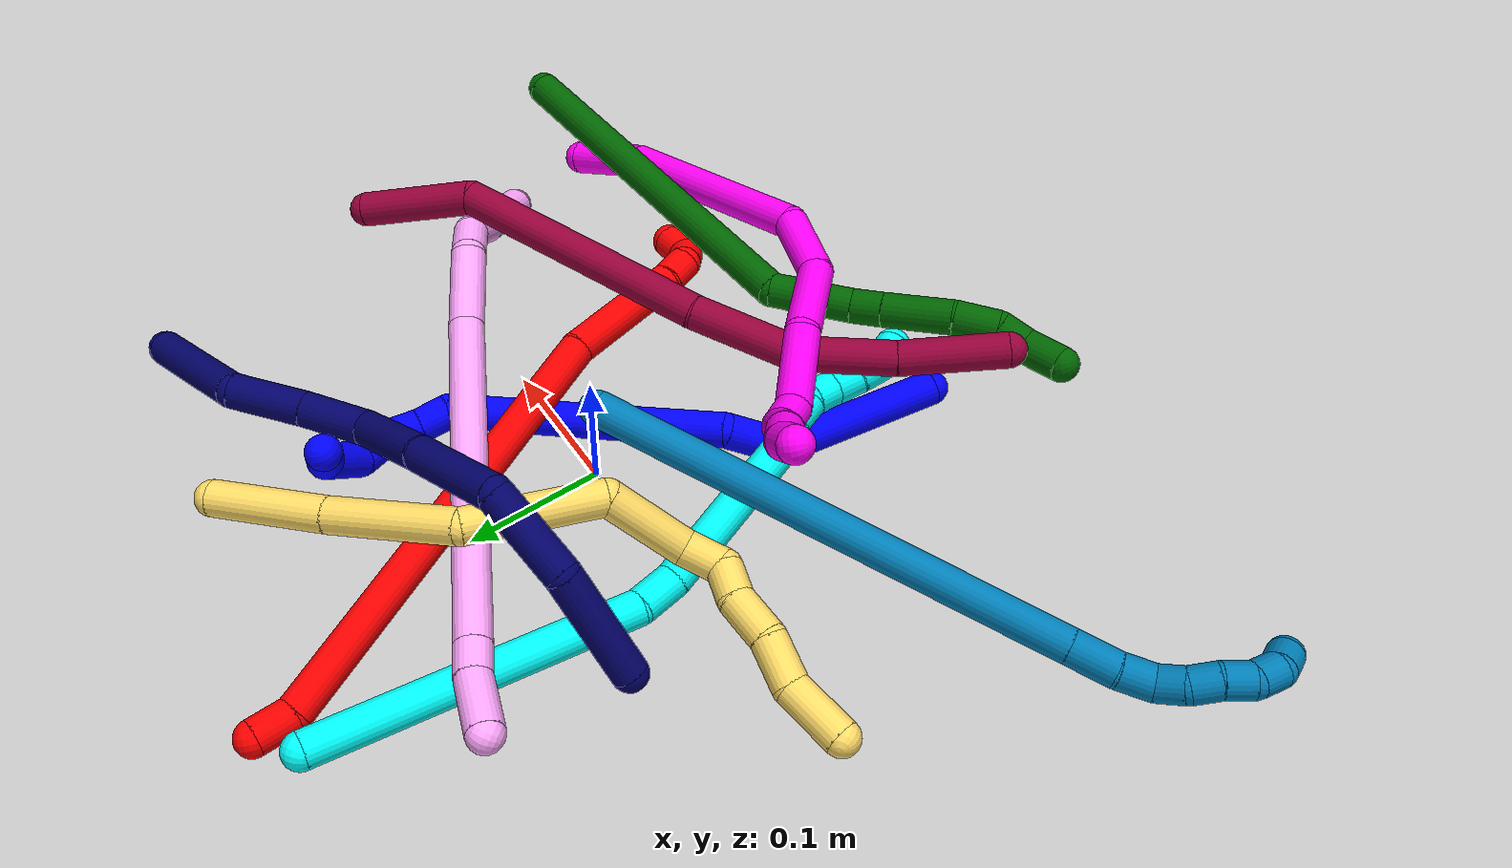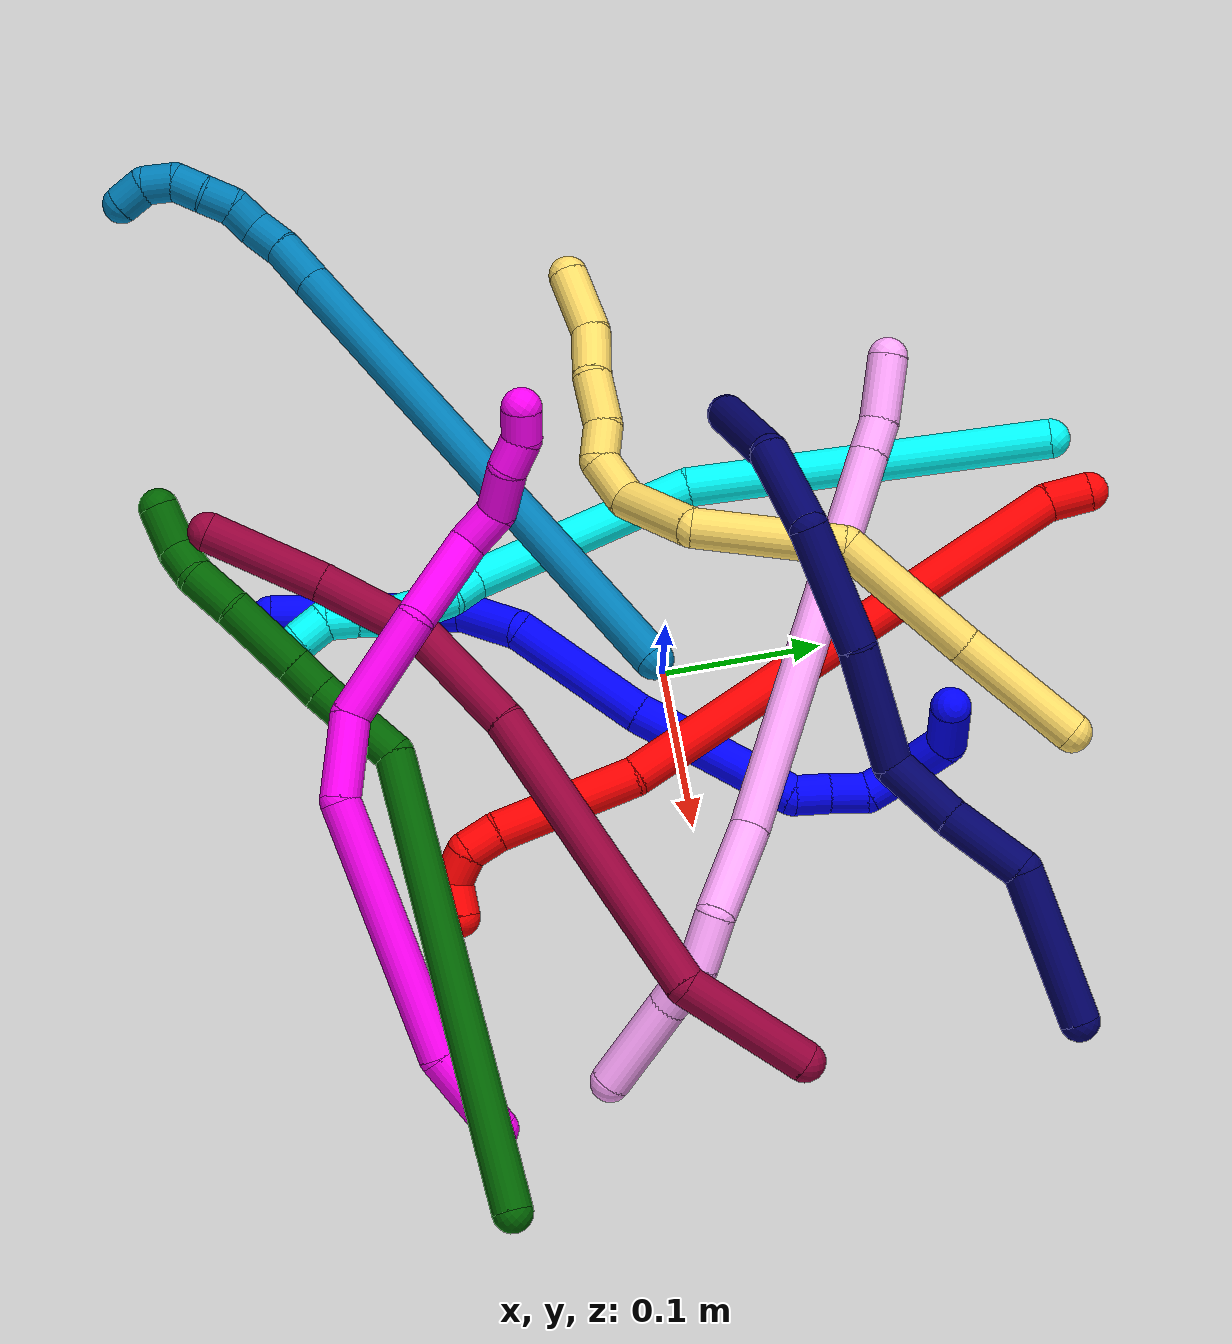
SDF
<sdf version="1.7">
 <world name="default">
  <plugin name="TubeGeneratorPlugin" filename="libtube_generator_plugin.so"/>
  <model name="photoneo_s_sensor">
   <static>1</static>
   <pose>0 0 2 1.57079 1.57079 3.14159</pose>
   <link name="link">
    <inertial><mass>0.1</mass></inertial>
    <sensor name="sensor" type="depth">
     <update_rate>30</update_rate>
     <camera>
      <horizontal_fov>1.22</horizontal_fov>
      <image><width>1920</width><height>1200</height><format>B8G8R8</format></image>
      <clip><near>0.1</near><far>4</far></clip>
      <depth_camera><output>points</output></depth_camera>
     </camera>
     <plugin name="camera_plugin" filename="libgazebo_ros_depth_camera.so">
      <baseline>0.2</baseline>
      <alwaysOn>1</alwaysOn>
      <updateRate>0.0</updateRate>
      <cameraName>camera_ir</cameraName>
      <imageTopicName>/camera/color/image_raw</imageTopicName>
      <cameraInfoTopicName>/camera/color/camera_info</cameraInfoTopicName>
      <depthImageTopicName>/camera/depth/image_raw</depthImageTopicName>
      <depthImageCameraInfoTopicName>/camera/depth/camera_info</depthImageCameraInfoTopicName>
      <pointCloudTopicName>/camera/depth/points</pointCloudTopicName>
      <frameName>fr_optical</frameName>
      <pointCloudCutoff>0.1</pointCloudCutoff>
      <pointCloudCutoffMax>2.0</pointCloudCutoffMax>
      <distortionK1>0</distortionK1>
      <distortionK2>0</distortionK2>
      <distortionK3>0</distortionK3>
      <distortionT1>0</distortionT1>
      <distortionT2>0</distortionT2>
      <CxPrime>0</CxPrime>
      <Cx>0</Cx>
      <Cy>0</Cy>
      <focalLength>0</focalLength>
      <hackBaseline>0</hackBaseline>
     </plugin>
    </sensor>
   </link>
  </model>
  <gravity>0 0 -9.8</gravity>
  <magnetic_field>6e-06 2.3e-05 -4.2e-05</magnetic_field>
  <atmosphere type="adiabatic"/>
  <physics name="default_physics" default="0" type="ode">
   <max_step_size>0.003</max_step_size>
   <real_time_factor>1</real_time_factor>
   <real_time_update_rate>1000</real_time_update_rate>
   <max_contacts>10000</max_contacts>
   <ode>
    <solver>
     <type>quick</type>
     <iters>100</iters>
     <sor>1.3</sor>
     <use_dynamic_moi_rescaling>0</use_dynamic_moi_rescaling>
    </solver>
    <constraints>
     <contact_max_correcting_vel>0</contact_max_correcting_vel>
     <contact_surface_layer>0.001</contact_surface_layer>
     <cfm>0</cfm>
     <erp>0.2</erp>
    </constraints>
   </ode>
  </physics>
  <scene><ambient>0.4 0.4 0.4 1</ambient><background>0.7 0.7 0.7 1</background><shadows>0</shadows></scene>
  <audio><device>default</device></audio>
  <spherical_coordinates>
   <surface_model>EARTH_WGS84</surface_model>
   <latitude_deg>0</latitude_deg>
   <longitude_deg>0</longitude_deg>
   <elevation>0</elevation>
   <heading_deg>0</heading_deg>
  </spherical_coordinates>
  <model name="bin">
   <static>1</static>
   <link name="bottom">
    <collision name="collision-bottom">
     <pose>0 0 -0.01 0 -0 0</pose>
     <geometry><box><size>0.8 0.6 0.02</size></box></geometry>
     <surface>
      <friction><ode><mu>100</mu><mu2>100</mu2></ode></friction>
      <contact><collide_bitmask>65535</collide_bitmask></contact>
     </surface>
    </collision>
   </link>
   <link name="west_wall">
    <collision name="collision-west_wall">
     <pose>-0.41 0 0.1 0 -0 0</pose>
     <geometry><box><size>0.02 0.6 0.2</size></box></geometry>
     <surface>
      <friction><ode><mu>100</mu><mu2>100</mu2></ode></friction>
      <contact><collide_bitmask>65535</collide_bitmask></contact>
     </surface>
    </collision>
   </link>
   <link name="east_wall">
    <collision name="collision-east_wall">
     <pose>0.41 0 0.1 0 -0 0</pose>
     <geometry><box><size>0.02 0.6 0.2</size></box></geometry>
     <surface>
      <friction><ode><mu>100</mu><mu2>100</mu2></ode></friction>
      <contact><collide_bitmask>65535</collide_bitmask></contact>
     </surface>
    </collision>
   </link>
   <link name="south_wall">
    <collision name="collision-south_wall">
     <pose>0 -0.31 0.1 0 -0 0</pose>
     <geometry><box><size>0.8 0.02 0.2</size></box></geometry>
     <surface>
      <friction><ode><mu>100</mu><mu2>100</mu2></ode></friction>
      <contact><collide_bitmask>65535</collide_bitmask></contact>
     </surface>
    </collision>
   </link>
   <link name="north_wall">
    <collision name="collision-north_wall">
     <pose>0 0.31 0.1 0 -0 0</pose>
     <geometry><box><size>0.8 0.02 0.2</size></box></geometry>
     <surface>
      <friction><ode><mu>100</mu><mu2>100</mu2></ode></friction>
      <contact><collide_bitmask>65535</collide_bitmask></contact>
     </surface>
    </collision>
   </link>
  </model>
  <model name="1">
   <static>0</static>
   <link name="1">
    <collision name="collision-cylinder-e_1_1_4">
     <pose>0.011512 0.057316 0.009499 -1.40655 0.195605 -0.166004</pose>
     <geometry><cylinder><radius>0.0125</radius><length>0.118455</length></cylinder></geometry>
     <surface>
      <friction><ode><mu>1.16</mu><mu2>1.16</mu2><slip1>0</slip1><slip2>0</slip2></ode></friction>
      <contact><ode><kp>1e+06</kp><kd>1</kd><max_vel>0</max_vel><min_depth>0.001</min_depth></ode></contact>
     </surface>
    </collision>
    <visual name="visual-cylinder-e_1_1_4">
     <pose>0.011512 0.057316 0.009499 -1.40655 0.195605 -0.166004</pose>
     <geometry><cylinder><radius>0.0125</radius><length>0.118455</length></cylinder></geometry>
     <material><ambient>0 0 1 1</ambient></material>
    </visual>
    <collision name="collision-cylinder-e_2_4_5">
     <pose>0.033314 0.128475 0.031853 -0.82238 0.498822 -0.221228</pose>
     <geometry><cylinder><radius>0.0125</radius><length>0.043024</length></cylinder></geometry>
     <surface>
      <friction><ode><mu>1.16</mu><mu2>1.16</mu2><slip1>0</slip1><slip2>0</slip2></ode></friction>
      <contact><ode><kp>1e+06</kp><kd>1</kd><max_vel>0</max_vel><min_depth>0.001</min_depth></ode></contact>
     </surface>
    </collision>
    <visual name="visual-cylinder-e_2_4_5">
     <pose>0.033314 0.128475 0.031853 -0.82238 0.498822 -0.221228</pose>
     <geometry><cylinder><radius>0.0125</radius><length>0.043024</length></cylinder></geometry>
     <material><ambient>0 0 1 1</ambient></material>
    </visual>
    <collision name="collision-cylinder-e_3_5_6">
     <pose>0.076528 0.172318 0.049597 -1.40927 0.825285 -0.712656</pose>
     <geometry><cylinder><radius>0.0125</radius><length>0.089617</length></cylinder></geometry>
     <surface>
      <friction><ode><mu>1.16</mu><mu2>1.16</mu2><slip1>0</slip1><slip2>0</slip2></ode></friction>
      <contact><ode><kp>1e+06</kp><kd>1</kd><max_vel>0</max_vel><min_depth>0.001</min_depth></ode></contact>
     </surface>
    </collision>
    <visual name="visual-cylinder-e_3_5_6">
     <pose>0.076528 0.172318 0.049597 -1.40927 0.825285 -0.712656</pose>
     <geometry><cylinder><radius>0.0125</radius><length>0.089617</length></cylinder></geometry>
     <material><ambient>0 0 1 1</ambient></material>
    </visual>
    <collision name="collision-cylinder-e_4_6_7">
     <pose>0.144763 0.241333 0.066909 -1.26252 0.711664 -0.530579</pose>
     <geometry><cylinder><radius>0.0125</radius><length>0.10814</length></cylinder></geometry>
     <surface>
      <friction><ode><mu>1.16</mu><mu2>1.16</mu2><slip1>0</slip1><slip2>0</slip2></ode></friction>
      <contact><ode><kp>1e+06</kp><kd>1</kd><max_vel>0</max_vel><min_depth>0.001</min_depth></ode></contact>
     </surface>
    </collision>
    <visual name="visual-cylinder-e_4_6_7">
     <pose>0.144763 0.241333 0.066909 -1.26252 0.711664 -0.530579</pose>
     <geometry><cylinder><radius>0.0125</radius><length>0.10814</length></cylinder></geometry>
     <material><ambient>0 0 1 1</ambient></material>
    </visual>
    <collision name="collision-cylinder-e_5_7_8">
     <pose>0.181719 0.291596 0.079708 -1.53745 0.14497 -0.14023</pose>
     <geometry><cylinder><radius>0.0125</radius><length>0.022746</length></cylinder></geometry>
     <surface>
      <friction><ode><mu>1.16</mu><mu2>1.16</mu2><slip1>0</slip1><slip2>0</slip2></ode></friction>
      <contact><ode><kp>1e+06</kp><kd>1</kd><max_vel>0</max_vel><min_depth>0.001</min_depth></ode></contact>
     </surface>
    </collision>
    <visual name="visual-cylinder-e_5_7_8">
     <pose>0.181719 0.291596 0.079708 -1.53745 0.14497 -0.14023</pose>
     <geometry><cylinder><radius>0.0125</radius><length>0.022746</length></cylinder></geometry>
     <material><ambient>0 0 1 1</ambient></material>
    </visual>
    <collision name="collision-cylinder-e_6_8_9">
     <pose>0.185759 0.314366 0.082129 -1.39504 0.202022 -0.169478</pose>
     <geometry><cylinder><radius>0.0125</radius><length>0.023892</length></cylinder></geometry>
     <surface>
      <friction><ode><mu>1.16</mu><mu2>1.16</mu2><slip1>0</slip1><slip2>0</slip2></ode></friction>
      <contact><ode><kp>1e+06</kp><kd>1</kd><max_vel>0</max_vel><min_depth>0.001</min_depth></ode></contact>
     </surface>
    </collision>
    <visual name="visual-cylinder-e_6_8_9">
     <pose>0.185759 0.314366 0.082129 -1.39504 0.202022 -0.169478</pose>
     <geometry><cylinder><radius>0.0125</radius><length>0.023892</length></cylinder></geometry>
     <material><ambient>0 0 1 1</ambient></material>
    </visual>
    <collision name="collision-cylinder-e_7_9_10">
     <pose>0.183872 0.338181 0.087084 -1.33845 -0.326958 0.259486</pose>
     <geometry><cylinder><radius>0.0125</radius><length>0.026675</length></cylinder></geometry>
     <surface>
      <friction><ode><mu>1.16</mu><mu2>1.16</mu2><slip1>0</slip1><slip2>0</slip2></ode></friction>
      <contact><ode><kp>1e+06</kp><kd>1</kd><max_vel>0</max_vel><min_depth>0.001</min_depth></ode></contact>
     </surface>
    </collision>
    <visual name="visual-cylinder-e_7_9_10">
     <pose>0.183872 0.338181 0.087084 -1.33845 -0.326958 0.259486</pose>
     <geometry><cylinder><radius>0.0125</radius><length>0.026675</length></cylinder></geometry>
     <material><ambient>0 0 1 1</ambient></material>
    </visual>
    <collision name="collision-cylinder-e_8_10_11">
     <pose>0.174672 0.361281 0.103209 -0.685497 -0.28038 0.100624</pose>
     <geometry><cylinder><radius>0.0125</radius><length>0.035537</length></cylinder></geometry>
     <surface>
      <friction><ode><mu>1.16</mu><mu2>1.16</mu2><slip1>0</slip1><slip2>0</slip2></ode></friction>
      <contact><ode><kp>1e+06</kp><kd>1</kd><max_vel>0</max_vel><min_depth>0.001</min_depth></ode></contact>
     </surface>
    </collision>
    <visual name="visual-cylinder-e_8_10_11">
     <pose>0.174672 0.361281 0.103209 -0.685497 -0.28038 0.100624</pose>
     <geometry><cylinder><radius>0.0125</radius><length>0.035537</length></cylinder></geometry>
     <material><ambient>0 0 1 1</ambient></material>
    </visual>
    <collision name="collision-cylinder-e_9_11_2">
     <pose>0.16003 0.371981 0.129078 0.008617 -0.655353 -0.002929</pose>
     <geometry><cylinder><radius>0.0125</radius><length>0.031915</length></cylinder></geometry>
     <surface>
      <friction><ode><mu>1.16</mu><mu2>1.16</mu2><slip1>0</slip1><slip2>0</slip2></ode></friction>
      <contact><ode><kp>1e+06</kp><kd>1</kd><max_vel>0</max_vel><min_depth>0.001</min_depth></ode></contact>
     </surface>
    </collision>
    <visual name="visual-cylinder-e_9_11_2">
     <pose>0.16003 0.371981 0.129078 0.008617 -0.655353 -0.002929</pose>
     <geometry><cylinder><radius>0.0125</radius><length>0.031915</length></cylinder></geometry>
     <material><ambient>0 0 1 1</ambient></material>
    </visual>
    <collision name="collision-sphere-2">
     <pose>0.150305 0.371872 0.141729 0 -0 0</pose>
     <geometry><sphere><radius>0.0125</radius></sphere></geometry>
     <surface>
      <friction><ode><mu>1.16</mu><mu2>1.16</mu2><slip1>0</slip1><slip2>0</slip2></ode></friction>
      <contact><ode><kp>1e+06</kp><kd>1</kd><max_vel>0</max_vel><min_depth>0.001</min_depth></ode></contact>
     </surface>
    </collision>
    <visual name="visual-sphere-2">
     <pose>0.150305 0.371872 0.141729 0 -0 0</pose>
     <geometry><sphere><radius>0.0125</radius></sphere></geometry>
     <material><ambient>0 0 1 1</ambient></material>
    </visual>
    <collision name="collision-sphere-11">
     <pose>0.169755 0.37209 0.116427 0 -0 0</pose>
     <geometry><sphere><radius>0.0125</radius></sphere></geometry>
     <surface>
      <friction><ode><mu>1.16</mu><mu2>1.16</mu2><slip1>0</slip1><slip2>0</slip2></ode></friction>
      <contact><ode><kp>1e+06</kp><kd>1</kd><max_vel>0</max_vel><min_depth>0.001</min_depth></ode></contact>
     </surface>
    </collision>
    <visual name="visual-sphere-11">
     <pose>0.169755 0.37209 0.116427 0 -0 0</pose>
     <geometry><sphere><radius>0.0125</radius></sphere></geometry>
     <material><ambient>0 0 1 1</ambient></material>
    </visual>
    <collision name="collision-sphere-10">
     <pose>0.179589 0.350472 0.089992 0 -0 0</pose>
     <geometry><sphere><radius>0.0125</radius></sphere></geometry>
     <surface>
      <friction><ode><mu>1.16</mu><mu2>1.16</mu2><slip1>0</slip1><slip2>0</slip2></ode></friction>
      <contact><ode><kp>1e+06</kp><kd>1</kd><max_vel>0</max_vel><min_depth>0.001</min_depth></ode></contact>
     </surface>
    </collision>
    <visual name="visual-sphere-10">
     <pose>0.179589 0.350472 0.089992 0 -0 0</pose>
     <geometry><sphere><radius>0.0125</radius></sphere></geometry>
     <material><ambient>0 0 1 1</ambient></material>
    </visual>
    <collision name="collision-sphere-9">
     <pose>0.188156 0.325889 0.084175 0 -0 0</pose>
     <geometry><sphere><radius>0.0125</radius></sphere></geometry>
     <surface>
      <friction><ode><mu>1.16</mu><mu2>1.16</mu2><slip1>0</slip1><slip2>0</slip2></ode></friction>
      <contact><ode><kp>1e+06</kp><kd>1</kd><max_vel>0</max_vel><min_depth>0.001</min_depth></ode></contact>
     </surface>
    </collision>
    <visual name="visual-sphere-9">
     <pose>0.188156 0.325889 0.084175 0 -0 0</pose>
     <geometry><sphere><radius>0.0125</radius></sphere></geometry>
     <material><ambient>0 0 1 1</ambient></material>
    </visual>
    <collision name="collision-sphere-4">
     <pose>0.023023 0.114633 0.018999 0 -0 0</pose>
     <geometry><sphere><radius>0.0125</radius></sphere></geometry>
     <surface>
      <friction><ode><mu>1.16</mu><mu2>1.16</mu2><slip1>0</slip1><slip2>0</slip2></ode></friction>
      <contact><ode><kp>1e+06</kp><kd>1</kd><max_vel>0</max_vel><min_depth>0.001</min_depth></ode></contact>
     </surface>
    </collision>
    <visual name="visual-sphere-4">
     <pose>0.023023 0.114633 0.018999 0 -0 0</pose>
     <geometry><sphere><radius>0.0125</radius></sphere></geometry>
     <material><ambient>0 0 1 1</ambient></material>
    </visual>
    <collision name="collision-sphere-1">
     <geometry><sphere><radius>0.0125</radius></sphere></geometry>
     <surface>
      <friction><ode><mu>1.16</mu><mu2>1.16</mu2><slip1>0</slip1><slip2>0</slip2></ode></friction>
      <contact><ode><kp>1e+06</kp><kd>1</kd><max_vel>0</max_vel><min_depth>0.001</min_depth></ode></contact>
     </surface>
    </collision>
    <visual name="visual-sphere-1">
     <geometry><sphere><radius>0.0125</radius></sphere></geometry>
     <material><ambient>0 0 1 1</ambient></material>
    </visual>
    <collision name="collision-sphere-8">
     <pose>0.183362 0.302844 0.080083 0 -0 0</pose>
     <geometry><sphere><radius>0.0125</radius></sphere></geometry>
     <surface>
      <friction><ode><mu>1.16</mu><mu2>1.16</mu2><slip1>0</slip1><slip2>0</slip2></ode></friction>
      <contact><ode><kp>1e+06</kp><kd>1</kd><max_vel>0</max_vel><min_depth>0.001</min_depth></ode></contact>
     </surface>
    </collision>
    <visual name="visual-sphere-8">
     <pose>0.183362 0.302844 0.080083 0 -0 0</pose>
     <geometry><sphere><radius>0.0125</radius></sphere></geometry>
     <material><ambient>0 0 1 1</ambient></material>
    </visual>
    <collision name="collision-sphere-5">
     <pose>0.043605 0.142318 0.044708 0 -0 0</pose>
     <geometry><sphere><radius>0.0125</radius></sphere></geometry>
     <surface>
      <friction><ode><mu>1.16</mu><mu2>1.16</mu2><slip1>0</slip1><slip2>0</slip2></ode></friction>
      <contact><ode><kp>1e+06</kp><kd>1</kd><max_vel>0</max_vel><min_depth>0.001</min_depth></ode></contact>
     </surface>
    </collision>
    <visual name="visual-sphere-5">
     <pose>0.043605 0.142318 0.044708 0 -0 0</pose>
     <geometry><sphere><radius>0.0125</radius></sphere></geometry>
     <material><ambient>0 0 1 1</ambient></material>
    </visual>
    <collision name="collision-sphere-6">
     <pose>0.10945 0.202318 0.054485 0 -0 0</pose>
     <geometry><sphere><radius>0.0125</radius></sphere></geometry>
     <surface>
      <friction><ode><mu>1.16</mu><mu2>1.16</mu2><slip1>0</slip1><slip2>0</slip2></ode></friction>
      <contact><ode><kp>1e+06</kp><kd>1</kd><max_vel>0</max_vel><min_depth>0.001</min_depth></ode></contact>
     </surface>
    </collision>
    <visual name="visual-sphere-6">
     <pose>0.10945 0.202318 0.054485 0 -0 0</pose>
     <geometry><sphere><radius>0.0125</radius></sphere></geometry>
     <material><ambient>0 0 1 1</ambient></material>
    </visual>
    <collision name="collision-sphere-7">
     <pose>0.180076 0.280348 0.079332 0 -0 0</pose>
     <geometry><sphere><radius>0.0125</radius></sphere></geometry>
     <surface>
      <friction><ode><mu>1.16</mu><mu2>1.16</mu2><slip1>0</slip1><slip2>0</slip2></ode></friction>
      <contact><ode><kp>1e+06</kp><kd>1</kd><max_vel>0</max_vel><min_depth>0.001</min_depth></ode></contact>
     </surface>
    </collision>
    <visual name="visual-sphere-7">
     <pose>0.180076 0.280348 0.079332 0 -0 0</pose>
     <geometry><sphere><radius>0.0125</radius></sphere></geometry>
     <material><ambient>0 0 1 1</ambient></material>
    </visual>
    <inertial>
     <pose>0.100201 0.203464 0.056123 0 -0 0</pose>
     <mass>0.5</mass>
     <inertia>
      <ixx>0.000181</ixx>
      <ixy>0</ixy>
      <ixz>0</ixz>
      <iyy>7.9e-05</iyy>
      <iyz>0</iyz>
      <izz>-0.00041</izz>
     </inertia>
    </inertial>
   </link>
   <pose>-0.076896 -0.233269 0.014157 -0.147599 0.199568 0.039539</pose>
  </model>
  <model name="2">
   <static>0</static>
   <link name="2">
    <collision name="collision-cylinder-e_1_1_4">
     <pose>0.006431 -0.011737 -0.002852 1.8092 0.489246 0.614965</pose>
     <geometry><cylinder><radius>0.0125</radius><length>0.027367</length></cylinder></geometry>
     <surface>
      <friction><ode><mu>1.16</mu><mu2>1.16</mu2><slip1>0</slip1><slip2>0</slip2></ode></friction>
      <contact><ode><kp>1e+06</kp><kd>1</kd><max_vel>0</max_vel><min_depth>0.001</min_depth></ode></contact>
     </surface>
    </collision>
    <visual name="visual-cylinder-e_1_1_4">
     <pose>0.006431 -0.011737 -0.002852 1.8092 0.489246 0.614965</pose>
     <geometry><cylinder><radius>0.0125</radius><length>0.027367</length></cylinder></geometry>
     <material><ambient>1 0 0 1</ambient></material>
    </visual>
    <collision name="collision-cylinder-e_2_4_5">
     <pose>0.050204 -0.154172 -0.0881 2.13328 0.237149 0.425338</pose>
     <geometry><cylinder><radius>0.0125</radius><length>0.317903</length></cylinder></geometry>
     <surface>
      <friction><ode><mu>1.16</mu><mu2>1.16</mu2><slip1>0</slip1><slip2>0</slip2></ode></friction>
      <contact><ode><kp>1e+06</kp><kd>1</kd><max_vel>0</max_vel><min_depth>0.001</min_depth></ode></contact>
     </surface>
    </collision>
    <visual name="visual-cylinder-e_2_4_5">
     <pose>0.050204 -0.154172 -0.0881 2.13328 0.237149 0.425338</pose>
     <geometry><cylinder><radius>0.0125</radius><length>0.317903</length></cylinder></geometry>
     <material><ambient>1 0 0 1</ambient></material>
    </visual>
    <collision name="collision-cylinder-e_3_5_6">
     <pose>0.104975 -0.323395 -0.1859 1.9512 0.397669 0.578477</pose>
     <geometry><cylinder><radius>0.0125</radius><length>0.090004</length></cylinder></geometry>
     <surface>
      <friction><ode><mu>1.16</mu><mu2>1.16</mu2><slip1>0</slip1><slip2>0</slip2></ode></friction>
      <contact><ode><kp>1e+06</kp><kd>1</kd><max_vel>0</max_vel><min_depth>0.001</min_depth></ode></contact>
     </surface>
    </collision>
    <visual name="visual-cylinder-e_3_5_6">
     <pose>0.104975 -0.323395 -0.1859 1.9512 0.397669 0.578477</pose>
     <geometry><cylinder><radius>0.0125</radius><length>0.090004</length></cylinder></geometry>
     <material><ambient>1 0 0 1</ambient></material>
    </visual>
    <collision name="collision-cylinder-e_4_6_7">
     <pose>0.124622 -0.371669 -0.205431 1.97112 0.206615 0.310385</pose>
     <geometry><cylinder><radius>0.0125</radius><length>0.021633</length></cylinder></geometry>
     <surface>
      <friction><ode><mu>1.16</mu><mu2>1.16</mu2><slip1>0</slip1><slip2>0</slip2></ode></friction>
      <contact><ode><kp>1e+06</kp><kd>1</kd><max_vel>0</max_vel><min_depth>0.001</min_depth></ode></contact>
     </surface>
    </collision>
    <visual name="visual-cylinder-e_4_6_7">
     <pose>0.124622 -0.371669 -0.205431 1.97112 0.206615 0.310385</pose>
     <geometry><cylinder><radius>0.0125</radius><length>0.021633</length></cylinder></geometry>
     <material><ambient>1 0 0 1</ambient></material>
    </visual>
    <collision name="collision-cylinder-e_5_7_8">
     <pose>0.122685 -0.390793 -0.211556 1.78101 -0.409078 -0.501929</pose>
     <geometry><cylinder><radius>0.0125</radius><length>0.020895</length></cylinder></geometry>
     <surface>
      <friction><ode><mu>1.16</mu><mu2>1.16</mu2><slip1>0</slip1><slip2>0</slip2></ode></friction>
      <contact><ode><kp>1e+06</kp><kd>1</kd><max_vel>0</max_vel><min_depth>0.001</min_depth></ode></contact>
     </surface>
    </collision>
    <visual name="visual-cylinder-e_5_7_8">
     <pose>0.122685 -0.390793 -0.211556 1.78101 -0.409078 -0.501929</pose>
     <geometry><cylinder><radius>0.0125</radius><length>0.020895</length></cylinder></geometry>
     <material><ambient>1 0 0 1</ambient></material>
    </visual>
    <collision name="collision-cylinder-e_6_8_2">
     <pose>0.109726 -0.404436 -0.218797 2.45806 -0.916044 -1.89149</pose>
     <geometry><cylinder><radius>0.0125</radius><length>0.022198</length></cylinder></geometry>
     <surface>
      <friction><ode><mu>1.16</mu><mu2>1.16</mu2><slip1>0</slip1><slip2>0</slip2></ode></friction>
      <contact><ode><kp>1e+06</kp><kd>1</kd><max_vel>0</max_vel><min_depth>0.001</min_depth></ode></contact>
     </surface>
    </collision>
    <visual name="visual-cylinder-e_6_8_2">
     <pose>0.109726 -0.404436 -0.218797 2.45806 -0.916044 -1.89149</pose>
     <geometry><cylinder><radius>0.0125</radius><length>0.022198</length></cylinder></geometry>
     <material><ambient>1 0 0 1</ambient></material>
    </visual>
    <collision name="collision-sphere-2">
     <pose>0.100922 -0.408704 -0.224038 0 -0 0</pose>
     <geometry><sphere><radius>0.0125</radius></sphere></geometry>
     <surface>
      <friction><ode><mu>1.16</mu><mu2>1.16</mu2><slip1>0</slip1><slip2>0</slip2></ode></friction>
      <contact><ode><kp>1e+06</kp><kd>1</kd><max_vel>0</max_vel><min_depth>0.001</min_depth></ode></contact>
     </surface>
    </collision>
    <visual name="visual-sphere-2">
     <pose>0.100922 -0.408704 -0.224038 0 -0 0</pose>
     <geometry><sphere><radius>0.0125</radius></sphere></geometry>
     <material><ambient>1 0 0 1</ambient></material>
    </visual>
    <collision name="collision-sphere-4">
     <pose>0.012861 -0.023473 -0.005705 0 -0 0</pose>
     <geometry><sphere><radius>0.0125</radius></sphere></geometry>
     <surface>
      <friction><ode><mu>1.16</mu><mu2>1.16</mu2><slip1>0</slip1><slip2>0</slip2></ode></friction>
      <contact><ode><kp>1e+06</kp><kd>1</kd><max_vel>0</max_vel><min_depth>0.001</min_depth></ode></contact>
     </surface>
    </collision>
    <visual name="visual-sphere-4">
     <pose>0.012861 -0.023473 -0.005705 0 -0 0</pose>
     <geometry><sphere><radius>0.0125</radius></sphere></geometry>
     <material><ambient>1 0 0 1</ambient></material>
    </visual>
    <collision name="collision-sphere-1">
     <geometry><sphere><radius>0.0125</radius></sphere></geometry>
     <surface>
      <friction><ode><mu>1.16</mu><mu2>1.16</mu2><slip1>0</slip1><slip2>0</slip2></ode></friction>
      <contact><ode><kp>1e+06</kp><kd>1</kd><max_vel>0</max_vel><min_depth>0.001</min_depth></ode></contact>
     </surface>
    </collision>
    <visual name="visual-sphere-1">
     <geometry><sphere><radius>0.0125</radius></sphere></geometry>
     <material><ambient>1 0 0 1</ambient></material>
    </visual>
    <collision name="collision-sphere-8">
     <pose>0.11853 -0.400167 -0.213557 0 -0 0</pose>
     <geometry><sphere><radius>0.0125</radius></sphere></geometry>
     <surface>
      <friction><ode><mu>1.16</mu><mu2>1.16</mu2><slip1>0</slip1><slip2>0</slip2></ode></friction>
      <contact><ode><kp>1e+06</kp><kd>1</kd><max_vel>0</max_vel><min_depth>0.001</min_depth></ode></contact>
     </surface>
    </collision>
    <visual name="visual-sphere-8">
     <pose>0.11853 -0.400167 -0.213557 0 -0 0</pose>
     <geometry><sphere><radius>0.0125</radius></sphere></geometry>
     <material><ambient>1 0 0 1</ambient></material>
    </visual>
    <collision name="collision-sphere-5">
     <pose>0.087547 -0.284871 -0.170495 0 -0 0</pose>
     <geometry><sphere><radius>0.0125</radius></sphere></geometry>
     <surface>
      <friction><ode><mu>1.16</mu><mu2>1.16</mu2><slip1>0</slip1><slip2>0</slip2></ode></friction>
      <contact><ode><kp>1e+06</kp><kd>1</kd><max_vel>0</max_vel><min_depth>0.001</min_depth></ode></contact>
     </surface>
    </collision>
    <visual name="visual-sphere-5">
     <pose>0.087547 -0.284871 -0.170495 0 -0 0</pose>
     <geometry><sphere><radius>0.0125</radius></sphere></geometry>
     <material><ambient>1 0 0 1</ambient></material>
    </visual>
    <collision name="collision-sphere-6">
     <pose>0.122403 -0.36192 -0.201305 0 -0 0</pose>
     <geometry><sphere><radius>0.0125</radius></sphere></geometry>
     <surface>
      <friction><ode><mu>1.16</mu><mu2>1.16</mu2><slip1>0</slip1><slip2>0</slip2></ode></friction>
      <contact><ode><kp>1e+06</kp><kd>1</kd><max_vel>0</max_vel><min_depth>0.001</min_depth></ode></contact>
     </surface>
    </collision>
    <visual name="visual-sphere-6">
     <pose>0.122403 -0.36192 -0.201305 0 -0 0</pose>
     <geometry><sphere><radius>0.0125</radius></sphere></geometry>
     <material><ambient>1 0 0 1</ambient></material>
    </visual>
    <collision name="collision-sphere-7">
     <pose>0.126841 -0.381418 -0.209556 0 -0 0</pose>
     <geometry><sphere><radius>0.0125</radius></sphere></geometry>
     <surface>
      <friction><ode><mu>1.16</mu><mu2>1.16</mu2><slip1>0</slip1><slip2>0</slip2></ode></friction>
      <contact><ode><kp>1e+06</kp><kd>1</kd><max_vel>0</max_vel><min_depth>0.001</min_depth></ode></contact>
     </surface>
    </collision>
    <visual name="visual-sphere-7">
     <pose>0.126841 -0.381418 -0.209556 0 -0 0</pose>
     <geometry><sphere><radius>0.0125</radius></sphere></geometry>
     <material><ambient>1 0 0 1</ambient></material>
    </visual>
    <inertial>
     <pose>0.066559 -0.207247 -0.117077 0 -0 0</pose>
     <mass>0.5</mass>
     <inertia>
      <ixx>0.003555</ixx>
      <ixy>0</ixy>
      <ixz>0</ixz>
      <iyy>-1.3e-05</iyy>
      <iyz>0</iyz>
      <izz>0.001599</izz>
     </inertia>
    </inertial>
   </link>
   <pose>-0.06228 0.282837 0.020864 2.54214 -0.476847 -2.47833</pose>
  </model>
  <model name="3">
   <static>0</static>
   <link name="3">
    <collision name="collision-cylinder-e_1_1_4">
     <pose>0.026574 -0.08248 -0.074107 2.30277 0.235225 0.518108</pose>
     <geometry><cylinder><radius>0.0125</radius><length>0.228045</length></cylinder></geometry>
     <surface>
      <friction><ode><mu>1.16</mu><mu2>1.16</mu2><slip1>0</slip1><slip2>0</slip2></ode></friction>
      <contact><ode><kp>1e+06</kp><kd>1</kd><max_vel>0</max_vel><min_depth>0.001</min_depth></ode></contact>
     </surface>
    </collision>
    <visual name="visual-cylinder-e_1_1_4">
     <pose>0.026574 -0.08248 -0.074107 2.30277 0.235225 0.518108</pose>
     <geometry><cylinder><radius>0.0125</radius><length>0.228045</length></cylinder></geometry>
     <material><ambient>0.003922 1 0.996078 1</ambient></material>
    </visual>
    <collision name="collision-cylinder-e_2_4_5">
     <pose>0.056954 -0.178649 -0.154583 2.00621 0.246947 0.384413</pose>
     <geometry><cylinder><radius>0.0125</radius><length>0.031138</length></cylinder></geometry>
     <surface>
      <friction><ode><mu>1.16</mu><mu2>1.16</mu2><slip1>0</slip1><slip2>0</slip2></ode></friction>
      <contact><ode><kp>1e+06</kp><kd>1</kd><max_vel>0</max_vel><min_depth>0.001</min_depth></ode></contact>
     </surface>
    </collision>
    <visual name="visual-cylinder-e_2_4_5">
     <pose>0.056954 -0.178649 -0.154583 2.00621 0.246947 0.384413</pose>
     <geometry><cylinder><radius>0.0125</radius><length>0.031138</length></cylinder></geometry>
     <material><ambient>0.003922 1 0.996078 1</ambient></material>
    </visual>
    <collision name="collision-cylinder-e_3_5_6">
     <pose>0.059302 -0.249378 -0.18064 1.90318 -0.024155 -0.03389</pose>
     <geometry><cylinder><radius>0.0125</radius><length>0.120723</length></cylinder></geometry>
     <surface>
      <friction><ode><mu>1.16</mu><mu2>1.16</mu2><slip1>0</slip1><slip2>0</slip2></ode></friction>
      <contact><ode><kp>1e+06</kp><kd>1</kd><max_vel>0</max_vel><min_depth>0.001</min_depth></ode></contact>
     </surface>
    </collision>
    <visual name="visual-cylinder-e_3_5_6">
     <pose>0.059302 -0.249378 -0.18064 1.90318 -0.024155 -0.03389</pose>
     <geometry><cylinder><radius>0.0125</radius><length>0.120723</length></cylinder></geometry>
     <material><ambient>0.003922 1 0.996078 1</ambient></material>
    </visual>
    <collision name="collision-cylinder-e_4_6_7">
     <pose>0.05579 -0.316175 -0.201187 1.65838 -0.206774 -0.225572</pose>
     <geometry><cylinder><radius>0.0125</radius><length>0.020012</length></cylinder></geometry>
     <surface>
      <friction><ode><mu>1.16</mu><mu2>1.16</mu2><slip1>0</slip1><slip2>0</slip2></ode></friction>
      <contact><ode><kp>1e+06</kp><kd>1</kd><max_vel>0</max_vel><min_depth>0.001</min_depth></ode></contact>
     </surface>
    </collision>
    <visual name="visual-cylinder-e_4_6_7">
     <pose>0.05579 -0.316175 -0.201187 1.65838 -0.206774 -0.225572</pose>
     <geometry><cylinder><radius>0.0125</radius><length>0.020012</length></cylinder></geometry>
     <material><ambient>0.003922 1 0.996078 1</ambient></material>
    </visual>
    <collision name="collision-cylinder-e_5_7_8">
     <pose>0.052641 -0.33525 -0.205594 1.93477 -0.109328 -0.158466</pose>
     <geometry><cylinder><radius>0.0125</radius><length>0.020065</length></cylinder></geometry>
     <surface>
      <friction><ode><mu>1.16</mu><mu2>1.16</mu2><slip1>0</slip1><slip2>0</slip2></ode></friction>
      <contact><ode><kp>1e+06</kp><kd>1</kd><max_vel>0</max_vel><min_depth>0.001</min_depth></ode></contact>
     </surface>
    </collision>
    <visual name="visual-cylinder-e_5_7_8">
     <pose>0.052641 -0.33525 -0.205594 1.93477 -0.109328 -0.158466</pose>
     <geometry><cylinder><radius>0.0125</radius><length>0.020065</length></cylinder></geometry>
     <material><ambient>0.003922 1 0.996078 1</ambient></material>
    </visual>
    <collision name="collision-cylinder-e_6_8_9">
     <pose>0.054701 -0.352488 -0.214386 2.15553 0.320679 0.584763</pose>
     <geometry><cylinder><radius>0.0125</radius><length>0.020012</length></cylinder></geometry>
     <surface>
      <friction><ode><mu>1.16</mu><mu2>1.16</mu2><slip1>0</slip1><slip2>0</slip2></ode></friction>
      <contact><ode><kp>1e+06</kp><kd>1</kd><max_vel>0</max_vel><min_depth>0.001</min_depth></ode></contact>
     </surface>
    </collision>
    <visual name="visual-cylinder-e_6_8_9">
     <pose>0.054701 -0.352488 -0.214386 2.15553 0.320679 0.584763</pose>
     <geometry><cylinder><radius>0.0125</radius><length>0.020012</length></cylinder></geometry>
     <material><ambient>0.003922 1 0.996078 1</ambient></material>
    </visual>
    <collision name="collision-cylinder-e_7_9_10">
     <pose>0.057927 -0.367545 -0.22663 2.34657 0.007277 0.017332</pose>
     <geometry><cylinder><radius>0.0125</radius><length>0.020002</length></cylinder></geometry>
     <surface>
      <friction><ode><mu>1.16</mu><mu2>1.16</mu2><slip1>0</slip1><slip2>0</slip2></ode></friction>
      <contact><ode><kp>1e+06</kp><kd>1</kd><max_vel>0</max_vel><min_depth>0.001</min_depth></ode></contact>
     </surface>
    </collision>
    <visual name="visual-cylinder-e_7_9_10">
     <pose>0.057927 -0.367545 -0.22663 2.34657 0.007277 0.017332</pose>
     <geometry><cylinder><radius>0.0125</radius><length>0.020002</length></cylinder></geometry>
     <material><ambient>0.003922 1 0.996078 1</ambient></material>
    </visual>
    <collision name="collision-cylinder-e_8_10_11">
     <pose>0.058417 -0.382371 -0.240017 2.26389 0.041642 0.088671</pose>
     <geometry><cylinder><radius>0.0125</radius><length>0.020001</length></cylinder></geometry>
     <surface>
      <friction><ode><mu>1.16</mu><mu2>1.16</mu2><slip1>0</slip1><slip2>0</slip2></ode></friction>
      <contact><ode><kp>1e+06</kp><kd>1</kd><max_vel>0</max_vel><min_depth>0.001</min_depth></ode></contact>
     </surface>
    </collision>
    <visual name="visual-cylinder-e_8_10_11">
     <pose>0.058417 -0.382371 -0.240017 2.26389 0.041642 0.088671</pose>
     <geometry><cylinder><radius>0.0125</radius><length>0.020001</length></cylinder></geometry>
     <material><ambient>0.003922 1 0.996078 1</ambient></material>
    </visual>
    <collision name="collision-cylinder-e_9_11_2">
     <pose>0.061499 -0.399589 -0.247837 1.72026 0.269821 0.312834</pose>
     <geometry><cylinder><radius>0.0125</radius><length>0.020001</length></cylinder></geometry>
     <surface>
      <friction><ode><mu>1.16</mu><mu2>1.16</mu2><slip1>0</slip1><slip2>0</slip2></ode></friction>
      <contact><ode><kp>1e+06</kp><kd>1</kd><max_vel>0</max_vel><min_depth>0.001</min_depth></ode></contact>
     </surface>
    </collision>
    <visual name="visual-cylinder-e_9_11_2">
     <pose>0.061499 -0.399589 -0.247837 1.72026 0.269821 0.312834</pose>
     <geometry><cylinder><radius>0.0125</radius><length>0.020001</length></cylinder></geometry>
     <material><ambient>0.003922 1 0.996078 1</ambient></material>
    </visual>
    <collision name="collision-sphere-2">
     <pose>0.064164 -0.40912 -0.249272 0 -0 0</pose>
     <geometry><sphere><radius>0.0125</radius></sphere></geometry>
     <surface>
      <friction><ode><mu>1.16</mu><mu2>1.16</mu2><slip1>0</slip1><slip2>0</slip2></ode></friction>
      <contact><ode><kp>1e+06</kp><kd>1</kd><max_vel>0</max_vel><min_depth>0.001</min_depth></ode></contact>
     </surface>
    </collision>
    <visual name="visual-sphere-2">
     <pose>0.064164 -0.40912 -0.249272 0 -0 0</pose>
     <geometry><sphere><radius>0.0125</radius></sphere></geometry>
     <material><ambient>0.003922 1 0.996078 1</ambient></material>
    </visual>
    <collision name="collision-sphere-11">
     <pose>0.058833 -0.390057 -0.246401 0 -0 0</pose>
     <geometry><sphere><radius>0.0125</radius></sphere></geometry>
     <surface>
      <friction><ode><mu>1.16</mu><mu2>1.16</mu2><slip1>0</slip1><slip2>0</slip2></ode></friction>
      <contact><ode><kp>1e+06</kp><kd>1</kd><max_vel>0</max_vel><min_depth>0.001</min_depth></ode></contact>
     </surface>
    </collision>
    <visual name="visual-sphere-11">
     <pose>0.058833 -0.390057 -0.246401 0 -0 0</pose>
     <geometry><sphere><radius>0.0125</radius></sphere></geometry>
     <material><ambient>0.003922 1 0.996078 1</ambient></material>
    </visual>
    <collision name="collision-sphere-10">
     <pose>0.058 -0.374685 -0.233633 0 -0 0</pose>
     <geometry><sphere><radius>0.0125</radius></sphere></geometry>
     <surface>
      <friction><ode><mu>1.16</mu><mu2>1.16</mu2><slip1>0</slip1><slip2>0</slip2></ode></friction>
      <contact><ode><kp>1e+06</kp><kd>1</kd><max_vel>0</max_vel><min_depth>0.001</min_depth></ode></contact>
     </surface>
    </collision>
    <visual name="visual-sphere-10">
     <pose>0.058 -0.374685 -0.233633 0 -0 0</pose>
     <geometry><sphere><radius>0.0125</radius></sphere></geometry>
     <material><ambient>0.003922 1 0.996078 1</ambient></material>
    </visual>
    <collision name="collision-sphere-9">
     <pose>0.057855 -0.360406 -0.219627 0 -0 0</pose>
     <geometry><sphere><radius>0.0125</radius></sphere></geometry>
     <surface>
      <friction><ode><mu>1.16</mu><mu2>1.16</mu2><slip1>0</slip1><slip2>0</slip2></ode></friction>
      <contact><ode><kp>1e+06</kp><kd>1</kd><max_vel>0</max_vel><min_depth>0.001</min_depth></ode></contact>
     </surface>
    </collision>
    <visual name="visual-sphere-9">
     <pose>0.057855 -0.360406 -0.219627 0 -0 0</pose>
     <geometry><sphere><radius>0.0125</radius></sphere></geometry>
     <material><ambient>0.003922 1 0.996078 1</ambient></material>
    </visual>
    <collision name="collision-sphere-4">
     <pose>0.053149 -0.164961 -0.148215 0 -0 0</pose>
     <geometry><sphere><radius>0.0125</radius></sphere></geometry>
     <surface>
      <friction><ode><mu>1.16</mu><mu2>1.16</mu2><slip1>0</slip1><slip2>0</slip2></ode></friction>
      <contact><ode><kp>1e+06</kp><kd>1</kd><max_vel>0</max_vel><min_depth>0.001</min_depth></ode></contact>
     </surface>
    </collision>
    <visual name="visual-sphere-4">
     <pose>0.053149 -0.164961 -0.148215 0 -0 0</pose>
     <geometry><sphere><radius>0.0125</radius></sphere></geometry>
     <material><ambient>0.003922 1 0.996078 1</ambient></material>
    </visual>
    <collision name="collision-sphere-1">
     <geometry><sphere><radius>0.0125</radius></sphere></geometry>
     <surface>
      <friction><ode><mu>1.16</mu><mu2>1.16</mu2><slip1>0</slip1><slip2>0</slip2></ode></friction>
      <contact><ode><kp>1e+06</kp><kd>1</kd><max_vel>0</max_vel><min_depth>0.001</min_depth></ode></contact>
     </surface>
    </collision>
    <visual name="visual-sphere-1">
     <geometry><sphere><radius>0.0125</radius></sphere></geometry>
     <material><ambient>0.003922 1 0.996078 1</ambient></material>
    </visual>
    <collision name="collision-sphere-8">
     <pose>0.051547 -0.344569 -0.209144 0 -0 0</pose>
     <geometry><sphere><radius>0.0125</radius></sphere></geometry>
     <surface>
      <friction><ode><mu>1.16</mu><mu2>1.16</mu2><slip1>0</slip1><slip2>0</slip2></ode></friction>
      <contact><ode><kp>1e+06</kp><kd>1</kd><max_vel>0</max_vel><min_depth>0.001</min_depth></ode></contact>
     </surface>
    </collision>
    <visual name="visual-sphere-8">
     <pose>0.051547 -0.344569 -0.209144 0 -0 0</pose>
     <geometry><sphere><radius>0.0125</radius></sphere></geometry>
     <material><ambient>0.003922 1 0.996078 1</ambient></material>
    </visual>
    <collision name="collision-sphere-5">
     <pose>0.06076 -0.192337 -0.16095 0 -0 0</pose>
     <geometry><sphere><radius>0.0125</radius></sphere></geometry>
     <surface>
      <friction><ode><mu>1.16</mu><mu2>1.16</mu2><slip1>0</slip1><slip2>0</slip2></ode></friction>
      <contact><ode><kp>1e+06</kp><kd>1</kd><max_vel>0</max_vel><min_depth>0.001</min_depth></ode></contact>
     </surface>
    </collision>
    <visual name="visual-sphere-5">
     <pose>0.06076 -0.192337 -0.16095 0 -0 0</pose>
     <geometry><sphere><radius>0.0125</radius></sphere></geometry>
     <material><ambient>0.003922 1 0.996078 1</ambient></material>
    </visual>
    <collision name="collision-sphere-6">
     <pose>0.057844 -0.306419 -0.20033 0 -0 0</pose>
     <geometry><sphere><radius>0.0125</radius></sphere></geometry>
     <surface>
      <friction><ode><mu>1.16</mu><mu2>1.16</mu2><slip1>0</slip1><slip2>0</slip2></ode></friction>
      <contact><ode><kp>1e+06</kp><kd>1</kd><max_vel>0</max_vel><min_depth>0.001</min_depth></ode></contact>
     </surface>
    </collision>
    <visual name="visual-sphere-6">
     <pose>0.057844 -0.306419 -0.20033 0 -0 0</pose>
     <geometry><sphere><radius>0.0125</radius></sphere></geometry>
     <material><ambient>0.003922 1 0.996078 1</ambient></material>
    </visual>
    <collision name="collision-sphere-7">
     <pose>0.053736 -0.32593 -0.202043 0 -0 0</pose>
     <geometry><sphere><radius>0.0125</radius></sphere></geometry>
     <surface>
      <friction><ode><mu>1.16</mu><mu2>1.16</mu2><slip1>0</slip1><slip2>0</slip2></ode></friction>
      <contact><ode><kp>1e+06</kp><kd>1</kd><max_vel>0</max_vel><min_depth>0.001</min_depth></ode></contact>
     </surface>
    </collision>
    <visual name="visual-sphere-7">
     <pose>0.053736 -0.32593 -0.202043 0 -0 0</pose>
     <geometry><sphere><radius>0.0125</radius></sphere></geometry>
     <material><ambient>0.003922 1 0.996078 1</ambient></material>
    </visual>
    <inertial>
     <pose>0.043635 -0.195155 -0.140506 0 -0 0</pose>
     <mass>0.5</mass>
     <inertia>
      <ixx>0.001487</ixx>
      <ixy>0</ixy>
      <ixz>0</ixz>
      <iyy>-0.000101</iyy>
      <iyz>0</iyz>
      <izz>0.000625</izz>
     </inertia>
    </inertial>
   </link>
   <pose>-0.095306 0.263286 0.038386 -1.74441 1.41759 -1.10339</pose>
  </model>
  <model name="4">
   <static>0</static>
   <link name="4">
    <collision name="collision-cylinder-e_1_1_4">
     <pose>0.017193 -0.006236 -0.010075 2.58736 0.967384 2.14907</pose>
     <geometry><cylinder><radius>0.0125</radius><length>0.04176</length></cylinder></geometry>
     <surface>
      <friction><ode><mu>1.16</mu><mu2>1.16</mu2><slip1>0</slip1><slip2>0</slip2></ode></friction>
      <contact><ode><kp>1e+06</kp><kd>1</kd><max_vel>0</max_vel><min_depth>0.001</min_depth></ode></contact>
     </surface>
    </collision>
    <visual name="visual-cylinder-e_1_1_4">
     <pose>0.017193 -0.006236 -0.010075 2.58736 0.967384 2.14907</pose>
     <geometry><cylinder><radius>0.0125</radius><length>0.04176</length></cylinder></geometry>
     <material><ambient>1 0.65098 0.996078 1</ambient></material>
    </visual>
    <collision name="collision-cylinder-e_2_4_5">
     <pose>0.044577 -0.01374 -0.024411 2.85217 1.15938 2.70357</pose>
     <geometry><cylinder><radius>0.0125</radius><length>0.022239</length></cylinder></geometry>
     <surface>
      <friction><ode><mu>1.16</mu><mu2>1.16</mu2><slip1>0</slip1><slip2>0</slip2></ode></friction>
      <contact><ode><kp>1e+06</kp><kd>1</kd><max_vel>0</max_vel><min_depth>0.001</min_depth></ode></contact>
     </surface>
    </collision>
    <visual name="visual-cylinder-e_2_4_5">
     <pose>0.044577 -0.01374 -0.024411 2.85217 1.15938 2.70357</pose>
     <geometry><cylinder><radius>0.0125</radius><length>0.022239</length></cylinder></geometry>
     <material><ambient>1 0.65098 0.996078 1</ambient></material>
    </visual>
    <collision name="collision-cylinder-e_3_5_6">
     <pose>0.169139 -0.026912 -0.078645 2.90776 1.14864 2.78248</pose>
     <geometry><cylinder><radius>0.0125</radius><length>0.250754</length></cylinder></geometry>
     <surface>
      <friction><ode><mu>1.16</mu><mu2>1.16</mu2><slip1>0</slip1><slip2>0</slip2></ode></friction>
      <contact><ode><kp>1e+06</kp><kd>1</kd><max_vel>0</max_vel><min_depth>0.001</min_depth></ode></contact>
     </surface>
    </collision>
    <visual name="visual-cylinder-e_3_5_6">
     <pose>0.169139 -0.026912 -0.078645 2.90776 1.14864 2.78248</pose>
     <geometry><cylinder><radius>0.0125</radius><length>0.250754</length></cylinder></geometry>
     <material><ambient>1 0.65098 0.996078 1</ambient></material>
    </visual>
    <collision name="collision-cylinder-e_4_6_7">
     <pose>0.31098 -0.036529 -0.140241 -2.94742 1.16367 -2.84761</pose>
     <geometry><cylinder><radius>0.0125</radius><length>0.059833</length></cylinder></geometry>
     <surface>
      <friction><ode><mu>1.16</mu><mu2>1.16</mu2><slip1>0</slip1><slip2>0</slip2></ode></friction>
      <contact><ode><kp>1e+06</kp><kd>1</kd><max_vel>0</max_vel><min_depth>0.001</min_depth></ode></contact>
     </surface>
    </collision>
    <visual name="visual-cylinder-e_4_6_7">
     <pose>0.31098 -0.036529 -0.140241 -2.94742 1.16367 -2.84761</pose>
     <geometry><cylinder><radius>0.0125</radius><length>0.059833</length></cylinder></geometry>
     <material><ambient>1 0.65098 0.996078 1</ambient></material>
    </visual>
    <collision name="collision-cylinder-e_5_7_8">
     <pose>0.35309 -0.040875 -0.156083 2.13741 1.07803 1.6563</pose>
     <geometry><cylinder><radius>0.0125</radius><length>0.03323</length></cylinder></geometry>
     <surface>
      <friction><ode><mu>1.16</mu><mu2>1.16</mu2><slip1>0</slip1><slip2>0</slip2></ode></friction>
      <contact><ode><kp>1e+06</kp><kd>1</kd><max_vel>0</max_vel><min_depth>0.001</min_depth></ode></contact>
     </surface>
    </collision>
    <visual name="visual-cylinder-e_5_7_8">
     <pose>0.35309 -0.040875 -0.156083 2.13741 1.07803 1.6563</pose>
     <geometry><cylinder><radius>0.0125</radius><length>0.03323</length></cylinder></geometry>
     <material><ambient>1 0.65098 0.996078 1</ambient></material>
    </visual>
    <collision name="collision-cylinder-e_6_8_9">
     <pose>0.380697 -0.056073 -0.157523 1.25709 0.963831 0.726639</pose>
     <geometry><cylinder><radius>0.0125</radius><length>0.031577</length></cylinder></geometry>
     <surface>
      <friction><ode><mu>1.16</mu><mu2>1.16</mu2><slip1>0</slip1><slip2>0</slip2></ode></friction>
      <contact><ode><kp>1e+06</kp><kd>1</kd><max_vel>0</max_vel><min_depth>0.001</min_depth></ode></contact>
     </surface>
    </collision>
    <visual name="visual-cylinder-e_6_8_9">
     <pose>0.380697 -0.056073 -0.157523 1.25709 0.963831 0.726639</pose>
     <geometry><cylinder><radius>0.0125</radius><length>0.031577</length></cylinder></geometry>
     <material><ambient>1 0.65098 0.996078 1</ambient></material>
    </visual>
    <collision name="collision-cylinder-e_7_9_2">
     <pose>0.420318 -0.078664 -0.151392 1.33619 1.07487 0.879212</pose>
     <geometry><cylinder><radius>0.0125</radius><length>0.060606</length></cylinder></geometry>
     <surface>
      <friction><ode><mu>1.16</mu><mu2>1.16</mu2><slip1>0</slip1><slip2>0</slip2></ode></friction>
      <contact><ode><kp>1e+06</kp><kd>1</kd><max_vel>0</max_vel><min_depth>0.001</min_depth></ode></contact>
     </surface>
    </collision>
    <visual name="visual-cylinder-e_7_9_2">
     <pose>0.420318 -0.078664 -0.151392 1.33619 1.07487 0.879212</pose>
     <geometry><cylinder><radius>0.0125</radius><length>0.060606</length></cylinder></geometry>
     <material><ambient>1 0.65098 0.996078 1</ambient></material>
    </visual>
    <collision name="collision-sphere-2">
     <pose>0.44697 -0.092688 -0.14804 0 -0 0</pose>
     <geometry><sphere><radius>0.0125</radius></sphere></geometry>
     <surface>
      <friction><ode><mu>1.16</mu><mu2>1.16</mu2><slip1>0</slip1><slip2>0</slip2></ode></friction>
      <contact><ode><kp>1e+06</kp><kd>1</kd><max_vel>0</max_vel><min_depth>0.001</min_depth></ode></contact>
     </surface>
    </collision>
    <visual name="visual-sphere-2">
     <pose>0.44697 -0.092688 -0.14804 0 -0 0</pose>
     <geometry><sphere><radius>0.0125</radius></sphere></geometry>
     <material><ambient>1 0.65098 0.996078 1</ambient></material>
    </visual>
    <collision name="collision-sphere-9">
     <pose>0.393665 -0.064639 -0.154744 0 -0 0</pose>
     <geometry><sphere><radius>0.0125</radius></sphere></geometry>
     <surface>
      <friction><ode><mu>1.16</mu><mu2>1.16</mu2><slip1>0</slip1><slip2>0</slip2></ode></friction>
      <contact><ode><kp>1e+06</kp><kd>1</kd><max_vel>0</max_vel><min_depth>0.001</min_depth></ode></contact>
     </surface>
    </collision>
    <visual name="visual-sphere-9">
     <pose>0.393665 -0.064639 -0.154744 0 -0 0</pose>
     <geometry><sphere><radius>0.0125</radius></sphere></geometry>
     <material><ambient>1 0.65098 0.996078 1</ambient></material>
    </visual>
    <collision name="collision-sphere-4">
     <pose>0.034385 -0.012471 -0.020149 0 -0 0</pose>
     <geometry><sphere><radius>0.0125</radius></sphere></geometry>
     <surface>
      <friction><ode><mu>1.16</mu><mu2>1.16</mu2><slip1>0</slip1><slip2>0</slip2></ode></friction>
      <contact><ode><kp>1e+06</kp><kd>1</kd><max_vel>0</max_vel><min_depth>0.001</min_depth></ode></contact>
     </surface>
    </collision>
    <visual name="visual-sphere-4">
     <pose>0.034385 -0.012471 -0.020149 0 -0 0</pose>
     <geometry><sphere><radius>0.0125</radius></sphere></geometry>
     <material><ambient>1 0.65098 0.996078 1</ambient></material>
    </visual>
    <collision name="collision-sphere-1">
     <geometry><sphere><radius>0.0125</radius></sphere></geometry>
     <surface>
      <friction><ode><mu>1.16</mu><mu2>1.16</mu2><slip1>0</slip1><slip2>0</slip2></ode></friction>
      <contact><ode><kp>1e+06</kp><kd>1</kd><max_vel>0</max_vel><min_depth>0.001</min_depth></ode></contact>
     </surface>
    </collision>
    <visual name="visual-sphere-1">
     <geometry><sphere><radius>0.0125</radius></sphere></geometry>
     <material><ambient>1 0.65098 0.996078 1</ambient></material>
    </visual>
    <collision name="collision-sphere-8">
     <pose>0.367728 -0.047507 -0.160302 0 -0 0</pose>
     <geometry><sphere><radius>0.0125</radius></sphere></geometry>
     <surface>
      <friction><ode><mu>1.16</mu><mu2>1.16</mu2><slip1>0</slip1><slip2>0</slip2></ode></friction>
      <contact><ode><kp>1e+06</kp><kd>1</kd><max_vel>0</max_vel><min_depth>0.001</min_depth></ode></contact>
     </surface>
    </collision>
    <visual name="visual-sphere-8">
     <pose>0.367728 -0.047507 -0.160302 0 -0 0</pose>
     <geometry><sphere><radius>0.0125</radius></sphere></geometry>
     <material><ambient>1 0.65098 0.996078 1</ambient></material>
    </visual>
    <collision name="collision-sphere-5">
     <pose>0.054769 -0.01501 -0.028673 0 -0 0</pose>
     <geometry><sphere><radius>0.0125</radius></sphere></geometry>
     <surface>
      <friction><ode><mu>1.16</mu><mu2>1.16</mu2><slip1>0</slip1><slip2>0</slip2></ode></friction>
      <contact><ode><kp>1e+06</kp><kd>1</kd><max_vel>0</max_vel><min_depth>0.001</min_depth></ode></contact>
     </surface>
    </collision>
    <visual name="visual-sphere-5">
     <pose>0.054769 -0.01501 -0.028673 0 -0 0</pose>
     <geometry><sphere><radius>0.0125</radius></sphere></geometry>
     <material><ambient>1 0.65098 0.996078 1</ambient></material>
    </visual>
    <collision name="collision-sphere-6">
     <pose>0.283509 -0.038815 -0.128617 0 -0 0</pose>
     <geometry><sphere><radius>0.0125</radius></sphere></geometry>
     <surface>
      <friction><ode><mu>1.16</mu><mu2>1.16</mu2><slip1>0</slip1><slip2>0</slip2></ode></friction>
      <contact><ode><kp>1e+06</kp><kd>1</kd><max_vel>0</max_vel><min_depth>0.001</min_depth></ode></contact>
     </surface>
    </collision>
    <visual name="visual-sphere-6">
     <pose>0.283509 -0.038815 -0.128617 0 -0 0</pose>
     <geometry><sphere><radius>0.0125</radius></sphere></geometry>
     <material><ambient>1 0.65098 0.996078 1</ambient></material>
    </visual>
    <collision name="collision-sphere-7">
     <pose>0.338451 -0.034244 -0.151864 0 -0 0</pose>
     <geometry><sphere><radius>0.0125</radius></sphere></geometry>
     <surface>
      <friction><ode><mu>1.16</mu><mu2>1.16</mu2><slip1>0</slip1><slip2>0</slip2></ode></friction>
      <contact><ode><kp>1e+06</kp><kd>1</kd><max_vel>0</max_vel><min_depth>0.001</min_depth></ode></contact>
     </surface>
    </collision>
    <visual name="visual-sphere-7">
     <pose>0.338451 -0.034244 -0.151864 0 -0 0</pose>
     <geometry><sphere><radius>0.0125</radius></sphere></geometry>
     <material><ambient>1 0.65098 0.996078 1</ambient></material>
    </visual>
    <inertial>
     <pose>0.223914 -0.034793 -0.096823 0 -0 0</pose>
     <mass>0.5</mass>
     <inertia>
      <ixx>-0.000272</ixx>
      <ixy>0</ixy>
      <ixz>0</ixz>
      <iyy>0.001551</iyy>
      <iyz>0</iyz>
      <izz>-0.001131</izz>
     </inertia>
    </inertial>
   </link>
   <pose>-0.157926 0.171063 0.062463 1.86725 0.012369 -0.913143</pose>
  </model>
  <model name="5">
   <static>0</static>
   <link name="5">
    <collision name="collision-cylinder-e_1_1_4">
     <pose>-0.02681 -0.032291 0.002354 1.49804 -0.691631 -0.646477</pose>
     <geometry><cylinder><radius>0.0125</radius><length>0.084072</length></cylinder></geometry>
     <surface>
      <friction><ode><mu>1.16</mu><mu2>1.16</mu2><slip1>0</slip1><slip2>0</slip2></ode></friction>
      <contact><ode><kp>1e+06</kp><kd>1</kd><max_vel>0</max_vel><min_depth>0.001</min_depth></ode></contact>
     </surface>
    </collision>
    <visual name="visual-cylinder-e_1_1_4">
     <pose>-0.02681 -0.032291 0.002354 1.49804 -0.691631 -0.646477</pose>
     <geometry><cylinder><radius>0.0125</radius><length>0.084072</length></cylinder></geometry>
     <material><ambient>1 0.858824 0.4 1</ambient></material>
    </visual>
    <collision name="collision-cylinder-e_2_4_5">
     <pose>-0.080506 -0.102997 0.008243 1.47903 -0.60865 -0.55806</pose>
     <geometry><cylinder><radius>0.0125</radius><length>0.094044</length></cylinder></geometry>
     <surface>
      <friction><ode><mu>1.16</mu><mu2>1.16</mu2><slip1>0</slip1><slip2>0</slip2></ode></friction>
      <contact><ode><kp>1e+06</kp><kd>1</kd><max_vel>0</max_vel><min_depth>0.001</min_depth></ode></contact>
     </surface>
    </collision>
    <visual name="visual-cylinder-e_2_4_5">
     <pose>-0.080506 -0.102997 0.008243 1.47903 -0.60865 -0.55806</pose>
     <geometry><cylinder><radius>0.0125</radius><length>0.094044</length></cylinder></geometry>
     <material><ambient>1 0.858824 0.4 1</ambient></material>
    </visual>
    <collision name="collision-cylinder-e_3_5_6">
     <pose>-0.134337 -0.172401 -0.011085 2.20644 -0.610533 -1.11589</pose>
     <geometry><cylinder><radius>0.0125</radius><length>0.094001</length></cylinder></geometry>
     <surface>
      <friction><ode><mu>1.16</mu><mu2>1.16</mu2><slip1>0</slip1><slip2>0</slip2></ode></friction>
      <contact><ode><kp>1e+06</kp><kd>1</kd><max_vel>0</max_vel><min_depth>0.001</min_depth></ode></contact>
     </surface>
    </collision>
    <visual name="visual-cylinder-e_3_5_6">
     <pose>-0.134337 -0.172401 -0.011085 2.20644 -0.610533 -1.11589</pose>
     <geometry><cylinder><radius>0.0125</radius><length>0.094001</length></cylinder></geometry>
     <material><ambient>1 0.858824 0.4 1</ambient></material>
    </visual>
    <collision name="collision-cylinder-e_4_6_7">
     <pose>-0.192402 -0.206831 -0.03912 2.55447 -1.37374 -2.43527</pose>
     <geometry><cylinder><radius>0.0125</radius><length>0.063467</length></cylinder></geometry>
     <surface>
      <friction><ode><mu>1.16</mu><mu2>1.16</mu2><slip1>0</slip1><slip2>0</slip2></ode></friction>
      <contact><ode><kp>1e+06</kp><kd>1</kd><max_vel>0</max_vel><min_depth>0.001</min_depth></ode></contact>
     </surface>
    </collision>
    <visual name="visual-cylinder-e_4_6_7">
     <pose>-0.192402 -0.206831 -0.03912 2.55447 -1.37374 -2.43527</pose>
     <geometry><cylinder><radius>0.0125</radius><length>0.063467</length></cylinder></geometry>
     <material><ambient>1 0.858824 0.4 1</ambient></material>
    </visual>
    <collision name="collision-cylinder-e_5_7_8">
     <pose>-0.234296 -0.219417 -0.039709 1.10612 -0.811424 -0.518401</pose>
     <geometry><cylinder><radius>0.0125</radius><length>0.029714</length></cylinder></geometry>
     <surface>
      <friction><ode><mu>1.16</mu><mu2>1.16</mu2><slip1>0</slip1><slip2>0</slip2></ode></friction>
      <contact><ode><kp>1e+06</kp><kd>1</kd><max_vel>0</max_vel><min_depth>0.001</min_depth></ode></contact>
     </surface>
    </collision>
    <visual name="visual-cylinder-e_5_7_8">
     <pose>-0.234296 -0.219417 -0.039709 1.10612 -0.811424 -0.518401</pose>
     <geometry><cylinder><radius>0.0125</radius><length>0.029714</length></cylinder></geometry>
     <material><ambient>1 0.858824 0.4 1</ambient></material>
    </visual>
    <collision name="collision-cylinder-e_6_8_9">
     <pose>-0.252293 -0.230018 -0.02553 0.150702 -0.639727 -0.050003</pose>
     <geometry><cylinder><radius>0.0125</radius><length>0.024194</length></cylinder></geometry>
     <surface>
      <friction><ode><mu>1.16</mu><mu2>1.16</mu2><slip1>0</slip1><slip2>0</slip2></ode></friction>
      <contact><ode><kp>1e+06</kp><kd>1</kd><max_vel>0</max_vel><min_depth>0.001</min_depth></ode></contact>
     </surface>
    </collision>
    <visual name="visual-cylinder-e_6_8_9">
     <pose>-0.252293 -0.230018 -0.02553 0.150702 -0.639727 -0.050003</pose>
     <geometry><cylinder><radius>0.0125</radius><length>0.024194</length></cylinder></geometry>
     <material><ambient>1 0.858824 0.4 1</ambient></material>
    </visual>
    <collision name="collision-cylinder-e_7_9_10">
     <pose>-0.271214 -0.23772 -0.005525 0.540406 -0.766913 -0.222556</pose>
     <geometry><cylinder><radius>0.0125</radius><length>0.03372</length></cylinder></geometry>
     <surface>
      <friction><ode><mu>1.16</mu><mu2>1.16</mu2><slip1>0</slip1><slip2>0</slip2></ode></friction>
      <contact><ode><kp>1e+06</kp><kd>1</kd><max_vel>0</max_vel><min_depth>0.001</min_depth></ode></contact>
     </surface>
    </collision>
    <visual name="visual-cylinder-e_7_9_10">
     <pose>-0.271214 -0.23772 -0.005525 0.540406 -0.766913 -0.222556</pose>
     <geometry><cylinder><radius>0.0125</radius><length>0.03372</length></cylinder></geometry>
     <material><ambient>1 0.858824 0.4 1</ambient></material>
    </visual>
    <collision name="collision-cylinder-e_8_10_11">
     <pose>-0.295523 -0.2452 0.01587 0.111795 -0.851006 -0.050706</pose>
     <geometry><cylinder><radius>0.0125</radius><length>0.033538</length></cylinder></geometry>
     <surface>
      <friction><ode><mu>1.16</mu><mu2>1.16</mu2><slip1>0</slip1><slip2>0</slip2></ode></friction>
      <contact><ode><kp>1e+06</kp><kd>1</kd><max_vel>0</max_vel><min_depth>0.001</min_depth></ode></contact>
     </surface>
    </collision>
    <visual name="visual-cylinder-e_8_10_11">
     <pose>-0.295523 -0.2452 0.01587 0.111795 -0.851006 -0.050706</pose>
     <geometry><cylinder><radius>0.0125</radius><length>0.033538</length></cylinder></geometry>
     <material><ambient>1 0.858824 0.4 1</ambient></material>
    </visual>
    <collision name="collision-cylinder-e_9_11_2">
     <pose>-0.325271 -0.254534 0.037261 0.661561 -0.915 -0.334968</pose>
     <geometry><cylinder><radius>0.0125</radius><length>0.04325</length></cylinder></geometry>
     <surface>
      <friction><ode><mu>1.16</mu><mu2>1.16</mu2><slip1>0</slip1><slip2>0</slip2></ode></friction>
      <contact><ode><kp>1e+06</kp><kd>1</kd><max_vel>0</max_vel><min_depth>0.001</min_depth></ode></contact>
     </surface>
    </collision>
    <visual name="visual-cylinder-e_9_11_2">
     <pose>-0.325271 -0.254534 0.037261 0.661561 -0.915 -0.334968</pose>
     <geometry><cylinder><radius>0.0125</radius><length>0.04325</length></cylinder></geometry>
     <material><ambient>1 0.858824 0.4 1</ambient></material>
    </visual>
    <collision name="collision-sphere-2">
     <pose>-0.342411 -0.262635 0.047665 0 -0 0</pose>
     <geometry><sphere><radius>0.0125</radius></sphere></geometry>
     <surface>
      <friction><ode><mu>1.16</mu><mu2>1.16</mu2><slip1>0</slip1><slip2>0</slip2></ode></friction>
      <contact><ode><kp>1e+06</kp><kd>1</kd><max_vel>0</max_vel><min_depth>0.001</min_depth></ode></contact>
     </surface>
    </collision>
    <visual name="visual-sphere-2">
     <pose>-0.342411 -0.262635 0.047665 0 -0 0</pose>
     <geometry><sphere><radius>0.0125</radius></sphere></geometry>
     <material><ambient>1 0.858824 0.4 1</ambient></material>
    </visual>
    <collision name="collision-sphere-11">
     <pose>-0.308132 -0.246433 0.026856 0 -0 0</pose>
     <geometry><sphere><radius>0.0125</radius></sphere></geometry>
     <surface>
      <friction><ode><mu>1.16</mu><mu2>1.16</mu2><slip1>0</slip1><slip2>0</slip2></ode></friction>
      <contact><ode><kp>1e+06</kp><kd>1</kd><max_vel>0</max_vel><min_depth>0.001</min_depth></ode></contact>
     </surface>
    </collision>
    <visual name="visual-sphere-11">
     <pose>-0.308132 -0.246433 0.026856 0 -0 0</pose>
     <geometry><sphere><radius>0.0125</radius></sphere></geometry>
     <material><ambient>1 0.858824 0.4 1</ambient></material>
    </visual>
    <collision name="collision-sphere-10">
     <pose>-0.282914 -0.243966 0.004885 0 -0 0</pose>
     <geometry><sphere><radius>0.0125</radius></sphere></geometry>
     <surface>
      <friction><ode><mu>1.16</mu><mu2>1.16</mu2><slip1>0</slip1><slip2>0</slip2></ode></friction>
      <contact><ode><kp>1e+06</kp><kd>1</kd><max_vel>0</max_vel><min_depth>0.001</min_depth></ode></contact>
     </surface>
    </collision>
    <visual name="visual-sphere-10">
     <pose>-0.282914 -0.243966 0.004885 0 -0 0</pose>
     <geometry><sphere><radius>0.0125</radius></sphere></geometry>
     <material><ambient>1 0.858824 0.4 1</ambient></material>
    </visual>
    <collision name="collision-sphere-9">
     <pose>-0.259515 -0.231475 -0.015935 0 -0 0</pose>
     <geometry><sphere><radius>0.0125</radius></sphere></geometry>
     <surface>
      <friction><ode><mu>1.16</mu><mu2>1.16</mu2><slip1>0</slip1><slip2>0</slip2></ode></friction>
      <contact><ode><kp>1e+06</kp><kd>1</kd><max_vel>0</max_vel><min_depth>0.001</min_depth></ode></contact>
     </surface>
    </collision>
    <visual name="visual-sphere-9">
     <pose>-0.259515 -0.231475 -0.015935 0 -0 0</pose>
     <geometry><sphere><radius>0.0125</radius></sphere></geometry>
     <material><ambient>1 0.858824 0.4 1</ambient></material>
    </visual>
    <collision name="collision-sphere-4">
     <pose>-0.053621 -0.064582 0.004707 0 -0 0</pose>
     <geometry><sphere><radius>0.0125</radius></sphere></geometry>
     <surface>
      <friction><ode><mu>1.16</mu><mu2>1.16</mu2><slip1>0</slip1><slip2>0</slip2></ode></friction>
      <contact><ode><kp>1e+06</kp><kd>1</kd><max_vel>0</max_vel><min_depth>0.001</min_depth></ode></contact>
     </surface>
    </collision>
    <visual name="visual-sphere-4">
     <pose>-0.053621 -0.064582 0.004707 0 -0 0</pose>
     <geometry><sphere><radius>0.0125</radius></sphere></geometry>
     <material><ambient>1 0.858824 0.4 1</ambient></material>
    </visual>
    <collision name="collision-sphere-1">
     <geometry><sphere><radius>0.0125</radius></sphere></geometry>
     <surface>
      <friction><ode><mu>1.16</mu><mu2>1.16</mu2><slip1>0</slip1><slip2>0</slip2></ode></friction>
      <contact><ode><kp>1e+06</kp><kd>1</kd><max_vel>0</max_vel><min_depth>0.001</min_depth></ode></contact>
     </surface>
    </collision>
    <visual name="visual-sphere-1">
     <geometry><sphere><radius>0.0125</radius></sphere></geometry>
     <material><ambient>1 0.858824 0.4 1</ambient></material>
    </visual>
    <collision name="collision-sphere-8">
     <pose>-0.245072 -0.228561 -0.035125 0 -0 0</pose>
     <geometry><sphere><radius>0.0125</radius></sphere></geometry>
     <surface>
      <friction><ode><mu>1.16</mu><mu2>1.16</mu2><slip1>0</slip1><slip2>0</slip2></ode></friction>
      <contact><ode><kp>1e+06</kp><kd>1</kd><max_vel>0</max_vel><min_depth>0.001</min_depth></ode></contact>
     </surface>
    </collision>
    <visual name="visual-sphere-8">
     <pose>-0.245072 -0.228561 -0.035125 0 -0 0</pose>
     <geometry><sphere><radius>0.0125</radius></sphere></geometry>
     <material><ambient>1 0.858824 0.4 1</ambient></material>
    </visual>
    <collision name="collision-sphere-5">
     <pose>-0.107392 -0.141413 0.011778 0 -0 0</pose>
     <geometry><sphere><radius>0.0125</radius></sphere></geometry>
     <surface>
      <friction><ode><mu>1.16</mu><mu2>1.16</mu2><slip1>0</slip1><slip2>0</slip2></ode></friction>
      <contact><ode><kp>1e+06</kp><kd>1</kd><max_vel>0</max_vel><min_depth>0.001</min_depth></ode></contact>
     </surface>
    </collision>
    <visual name="visual-sphere-5">
     <pose>-0.107392 -0.141413 0.011778 0 -0 0</pose>
     <geometry><sphere><radius>0.0125</radius></sphere></geometry>
     <material><ambient>1 0.858824 0.4 1</ambient></material>
    </visual>
    <collision name="collision-sphere-6">
     <pose>-0.161283 -0.203389 -0.033948 0 -0 0</pose>
     <geometry><sphere><radius>0.0125</radius></sphere></geometry>
     <surface>
      <friction><ode><mu>1.16</mu><mu2>1.16</mu2><slip1>0</slip1><slip2>0</slip2></ode></friction>
      <contact><ode><kp>1e+06</kp><kd>1</kd><max_vel>0</max_vel><min_depth>0.001</min_depth></ode></contact>
     </surface>
    </collision>
    <visual name="visual-sphere-6">
     <pose>-0.161283 -0.203389 -0.033948 0 -0 0</pose>
     <geometry><sphere><radius>0.0125</radius></sphere></geometry>
     <material><ambient>1 0.858824 0.4 1</ambient></material>
    </visual>
    <collision name="collision-sphere-7">
     <pose>-0.223521 -0.210273 -0.044293 0 -0 0</pose>
     <geometry><sphere><radius>0.0125</radius></sphere></geometry>
     <surface>
      <friction><ode><mu>1.16</mu><mu2>1.16</mu2><slip1>0</slip1><slip2>0</slip2></ode></friction>
      <contact><ode><kp>1e+06</kp><kd>1</kd><max_vel>0</max_vel><min_depth>0.001</min_depth></ode></contact>
     </surface>
    </collision>
    <visual name="visual-sphere-7">
     <pose>-0.223521 -0.210273 -0.044293 0 -0 0</pose>
     <geometry><sphere><radius>0.0125</radius></sphere></geometry>
     <material><ambient>1 0.858824 0.4 1</ambient></material>
    </visual>
    <inertial>
     <pose>-0.161709 -0.162133 -0.004784 0 -0 0</pose>
     <mass>0.5</mass>
     <inertia>
      <ixx>-2.3e-05</ixx>
      <ixy>0</ixy>
      <ixz>0</ixz>
      <iyy>-3.1e-05</iyy>
      <iyz>0</iyz>
      <izz>0.000319</izz>
     </inertia>
    </inertial>
   </link>
   <pose>0.094887 0.233862 0.04665 -1.17644 -0.698499 0.471186</pose>
  </model>
  <model name="6">
   <static>0</static>
   <link name="6">
    <collision name="collision-cylinder-e_1_1_4">
     <pose>-0.08357 -0.043943 -0.106606 2.75062 -0.62715 -2.04517</pose>
     <geometry><cylinder><radius>0.0125</radius><length>0.284814</length></cylinder></geometry>
     <surface>
      <friction><ode><mu>1.16</mu><mu2>1.16</mu2><slip1>0</slip1><slip2>0</slip2></ode></friction>
      <contact><ode><kp>1e+06</kp><kd>1</kd><max_vel>0</max_vel><min_depth>0.001</min_depth></ode></contact>
     </surface>
    </collision>
    <visual name="visual-cylinder-e_1_1_4">
     <pose>-0.08357 -0.043943 -0.106606 2.75062 -0.62715 -2.04517</pose>
     <geometry><cylinder><radius>0.0125</radius><length>0.284814</length></cylinder></geometry>
     <material><ambient>0 0.392157 0.003922 1</ambient></material>
    </visual>
    <collision name="collision-cylinder-e_2_4_5">
     <pose>-0.178343 -0.081102 -0.240082 -2.8943 -0.38417 2.00436</pose>
     <geometry><cylinder><radius>0.0125</radius><length>0.059784</length></cylinder></geometry>
     <surface>
      <friction><ode><mu>1.16</mu><mu2>1.16</mu2><slip1>0</slip1><slip2>0</slip2></ode></friction>
      <contact><ode><kp>1e+06</kp><kd>1</kd><max_vel>0</max_vel><min_depth>0.001</min_depth></ode></contact>
     </surface>
    </collision>
    <visual name="visual-cylinder-e_2_4_5">
     <pose>-0.178343 -0.081102 -0.240082 -2.8943 -0.38417 2.00436</pose>
     <geometry><cylinder><radius>0.0125</radius><length>0.059784</length></cylinder></geometry>
     <material><ambient>0 0.392157 0.003922 1</ambient></material>
    </visual>
    <collision name="collision-cylinder-e_3_5_6">
     <pose>-0.192643 -0.072918 -0.277829 -3.01351 -0.275191 2.27417</pose>
     <geometry><cylinder><radius>0.0125</radius><length>0.02279</length></cylinder></geometry>
     <surface>
      <friction><ode><mu>1.16</mu><mu2>1.16</mu2><slip1>0</slip1><slip2>0</slip2></ode></friction>
      <contact><ode><kp>1e+06</kp><kd>1</kd><max_vel>0</max_vel><min_depth>0.001</min_depth></ode></contact>
     </surface>
    </collision>
    <visual name="visual-cylinder-e_3_5_6">
     <pose>-0.192643 -0.072918 -0.277829 -3.01351 -0.275191 2.27417</pose>
     <geometry><cylinder><radius>0.0125</radius><length>0.02279</length></cylinder></geometry>
     <material><ambient>0 0.392157 0.003922 1</ambient></material>
    </visual>
    <collision name="collision-cylinder-e_4_6_7">
     <pose>-0.202283 -0.068003 -0.312813 -2.99686 -0.262404 2.13689</pose>
     <geometry><cylinder><radius>0.0125</radius><length>0.050453</length></cylinder></geometry>
     <surface>
      <friction><ode><mu>1.16</mu><mu2>1.16</mu2><slip1>0</slip1><slip2>0</slip2></ode></friction>
      <contact><ode><kp>1e+06</kp><kd>1</kd><max_vel>0</max_vel><min_depth>0.001</min_depth></ode></contact>
     </surface>
    </collision>
    <visual name="visual-cylinder-e_4_6_7">
     <pose>-0.202283 -0.068003 -0.312813 -2.99686 -0.262404 2.13689</pose>
     <geometry><cylinder><radius>0.0125</radius><length>0.050453</length></cylinder></geometry>
     <material><ambient>0 0.392157 0.003922 1</ambient></material>
    </visual>
    <collision name="collision-cylinder-e_5_7_8">
     <pose>-0.215157 -0.060994 -0.350663 -2.89252 -0.419874 2.07923</pose>
     <geometry><cylinder><radius>0.0125</radius><length>0.031056</length></cylinder></geometry>
     <surface>
      <friction><ode><mu>1.16</mu><mu2>1.16</mu2><slip1>0</slip1><slip2>0</slip2></ode></friction>
      <contact><ode><kp>1e+06</kp><kd>1</kd><max_vel>0</max_vel><min_depth>0.001</min_depth></ode></contact>
     </surface>
    </collision>
    <visual name="visual-cylinder-e_5_7_8">
     <pose>-0.215157 -0.060994 -0.350663 -2.89252 -0.419874 2.07923</pose>
     <geometry><cylinder><radius>0.0125</radius><length>0.031056</length></cylinder></geometry>
     <material><ambient>0 0.392157 0.003922 1</ambient></material>
    </visual>
    <collision name="collision-cylinder-e_6_8_9">
     <pose>-0.229149 -0.056283 -0.372029 -2.98342 -0.781586 2.76151</pose>
     <geometry><cylinder><radius>0.0125</radius><length>0.021754</length></cylinder></geometry>
     <surface>
      <friction><ode><mu>1.16</mu><mu2>1.16</mu2><slip1>0</slip1><slip2>0</slip2></ode></friction>
      <contact><ode><kp>1e+06</kp><kd>1</kd><max_vel>0</max_vel><min_depth>0.001</min_depth></ode></contact>
     </surface>
    </collision>
    <visual name="visual-cylinder-e_6_8_9">
     <pose>-0.229149 -0.056283 -0.372029 -2.98342 -0.781586 2.76151</pose>
     <geometry><cylinder><radius>0.0125</radius><length>0.021754</length></cylinder></geometry>
     <material><ambient>0 0.392157 0.003922 1</ambient></material>
    </visual>
    <collision name="collision-cylinder-e_7_9_2">
     <pose>-0.243628 -0.058053 -0.3923 2.90973 -0.483175 -2.25859</pose>
     <geometry><cylinder><radius>0.0125</radius><length>0.029349</length></cylinder></geometry>
     <surface>
      <friction><ode><mu>1.16</mu><mu2>1.16</mu2><slip1>0</slip1><slip2>0</slip2></ode></friction>
      <contact><ode><kp>1e+06</kp><kd>1</kd><max_vel>0</max_vel><min_depth>0.001</min_depth></ode></contact>
     </surface>
    </collision>
    <visual name="visual-cylinder-e_7_9_2">
     <pose>-0.243628 -0.058053 -0.3923 2.90973 -0.483175 -2.25859</pose>
     <geometry><cylinder><radius>0.0125</radius><length>0.029349</length></cylinder></geometry>
     <material><ambient>0 0.392157 0.003922 1</ambient></material>
    </visual>
    <collision name="collision-sphere-2">
     <pose>-0.250446 -0.061039 -0.404947 0 -0 0</pose>
     <geometry><sphere><radius>0.0125</radius></sphere></geometry>
     <surface>
      <friction><ode><mu>1.16</mu><mu2>1.16</mu2><slip1>0</slip1><slip2>0</slip2></ode></friction>
      <contact><ode><kp>1e+06</kp><kd>1</kd><max_vel>0</max_vel><min_depth>0.001</min_depth></ode></contact>
     </surface>
    </collision>
    <visual name="visual-sphere-2">
     <pose>-0.250446 -0.061039 -0.404947 0 -0 0</pose>
     <geometry><sphere><radius>0.0125</radius></sphere></geometry>
     <material><ambient>0 0.392157 0.003922 1</ambient></material>
    </visual>
    <collision name="collision-sphere-9">
     <pose>-0.23681 -0.055067 -0.379653 0 -0 0</pose>
     <geometry><sphere><radius>0.0125</radius></sphere></geometry>
     <surface>
      <friction><ode><mu>1.16</mu><mu2>1.16</mu2><slip1>0</slip1><slip2>0</slip2></ode></friction>
      <contact><ode><kp>1e+06</kp><kd>1</kd><max_vel>0</max_vel><min_depth>0.001</min_depth></ode></contact>
     </surface>
    </collision>
    <visual name="visual-sphere-9">
     <pose>-0.23681 -0.055067 -0.379653 0 -0 0</pose>
     <geometry><sphere><radius>0.0125</radius></sphere></geometry>
     <material><ambient>0 0.392157 0.003922 1</ambient></material>
    </visual>
    <collision name="collision-sphere-4">
     <pose>-0.16714 -0.087886 -0.213212 0 -0 0</pose>
     <geometry><sphere><radius>0.0125</radius></sphere></geometry>
     <surface>
      <friction><ode><mu>1.16</mu><mu2>1.16</mu2><slip1>0</slip1><slip2>0</slip2></ode></friction>
      <contact><ode><kp>1e+06</kp><kd>1</kd><max_vel>0</max_vel><min_depth>0.001</min_depth></ode></contact>
     </surface>
    </collision>
    <visual name="visual-sphere-4">
     <pose>-0.16714 -0.087886 -0.213212 0 -0 0</pose>
     <geometry><sphere><radius>0.0125</radius></sphere></geometry>
     <material><ambient>0 0.392157 0.003922 1</ambient></material>
    </visual>
    <collision name="collision-sphere-1">
     <geometry><sphere><radius>0.0125</radius></sphere></geometry>
     <surface>
      <friction><ode><mu>1.16</mu><mu2>1.16</mu2><slip1>0</slip1><slip2>0</slip2></ode></friction>
      <contact><ode><kp>1e+06</kp><kd>1</kd><max_vel>0</max_vel><min_depth>0.001</min_depth></ode></contact>
     </surface>
    </collision>
    <visual name="visual-sphere-1">
     <geometry><sphere><radius>0.0125</radius></sphere></geometry>
     <material><ambient>0 0.392157 0.003922 1</ambient></material>
    </visual>
    <collision name="collision-sphere-8">
     <pose>-0.221487 -0.057499 -0.364405 0 -0 0</pose>
     <geometry><sphere><radius>0.0125</radius></sphere></geometry>
     <surface>
      <friction><ode><mu>1.16</mu><mu2>1.16</mu2><slip1>0</slip1><slip2>0</slip2></ode></friction>
      <contact><ode><kp>1e+06</kp><kd>1</kd><max_vel>0</max_vel><min_depth>0.001</min_depth></ode></contact>
     </surface>
    </collision>
    <visual name="visual-sphere-8">
     <pose>-0.221487 -0.057499 -0.364405 0 -0 0</pose>
     <geometry><sphere><radius>0.0125</radius></sphere></geometry>
     <material><ambient>0 0.392157 0.003922 1</ambient></material>
    </visual>
    <collision name="collision-sphere-5">
     <pose>-0.189547 -0.074319 -0.266952 0 -0 0</pose>
     <geometry><sphere><radius>0.0125</radius></sphere></geometry>
     <surface>
      <friction><ode><mu>1.16</mu><mu2>1.16</mu2><slip1>0</slip1><slip2>0</slip2></ode></friction>
      <contact><ode><kp>1e+06</kp><kd>1</kd><max_vel>0</max_vel><min_depth>0.001</min_depth></ode></contact>
     </surface>
    </collision>
    <visual name="visual-sphere-5">
     <pose>-0.189547 -0.074319 -0.266952 0 -0 0</pose>
     <geometry><sphere><radius>0.0125</radius></sphere></geometry>
     <material><ambient>0 0.392157 0.003922 1</ambient></material>
    </visual>
    <collision name="collision-sphere-6">
     <pose>-0.195739 -0.071517 -0.288705 0 -0 0</pose>
     <geometry><sphere><radius>0.0125</radius></sphere></geometry>
     <surface>
      <friction><ode><mu>1.16</mu><mu2>1.16</mu2><slip1>0</slip1><slip2>0</slip2></ode></friction>
      <contact><ode><kp>1e+06</kp><kd>1</kd><max_vel>0</max_vel><min_depth>0.001</min_depth></ode></contact>
     </surface>
    </collision>
    <visual name="visual-sphere-6">
     <pose>-0.195739 -0.071517 -0.288705 0 -0 0</pose>
     <geometry><sphere><radius>0.0125</radius></sphere></geometry>
     <material><ambient>0 0.392157 0.003922 1</ambient></material>
    </visual>
    <collision name="collision-sphere-7">
     <pose>-0.208827 -0.06449 -0.336921 0 -0 0</pose>
     <geometry><sphere><radius>0.0125</radius></sphere></geometry>
     <surface>
      <friction><ode><mu>1.16</mu><mu2>1.16</mu2><slip1>0</slip1><slip2>0</slip2></ode></friction>
      <contact><ode><kp>1e+06</kp><kd>1</kd><max_vel>0</max_vel><min_depth>0.001</min_depth></ode></contact>
     </surface>
    </collision>
    <visual name="visual-sphere-7">
     <pose>-0.208827 -0.06449 -0.336921 0 -0 0</pose>
     <geometry><sphere><radius>0.0125</radius></sphere></geometry>
     <material><ambient>0 0.392157 0.003922 1</ambient></material>
    </visual>
    <inertial>
     <pose>-0.135754 -0.054559 -0.194654 0 -0 0</pose>
     <mass>0.5</mass>
     <inertia>
      <ixx>-0.002121</ixx>
      <ixy>0</ixy>
      <ixz>0</ixz>
      <iyy>-0.000142</iyy>
      <iyz>0</iyz>
      <izz>0.001711</izz>
     </inertia>
    </inertial>
   </link>
   <pose>0.319457 -0.150492 0.044386 -2.42785 -0.88977 -0.182396</pose>
  </model>
  <model name="7">
   <static>0</static>
   <link name="7">
    <collision name="collision-cylinder-e_1_1_4">
     <pose>-0.030804 0.023376 -0.030326 -2.4849 -0.677476 1.60439</pose>
     <geometry><cylinder><radius>0.0125</radius><length>0.098285</length></cylinder></geometry>
     <surface>
      <friction><ode><mu>1.16</mu><mu2>1.16</mu2><slip1>0</slip1><slip2>0</slip2></ode></friction>
      <contact><ode><kp>1e+06</kp><kd>1</kd><max_vel>0</max_vel><min_depth>0.001</min_depth></ode></contact>
     </surface>
    </collision>
    <visual name="visual-cylinder-e_1_1_4">
     <pose>-0.030804 0.023376 -0.030326 -2.4849 -0.677476 1.60439</pose>
     <geometry><cylinder><radius>0.0125</radius><length>0.098285</length></cylinder></geometry>
     <material><ambient>0.003922 0 0.403922 1</ambient></material>
    </visual>
    <collision name="collision-cylinder-e_2_4_5">
     <pose>-0.086398 0.056695 -0.062763 -1.77995 -1.18167 1.38327</pose>
     <geometry><cylinder><radius>0.0125</radius><length>0.053587</length></cylinder></geometry>
     <surface>
      <friction><ode><mu>1.16</mu><mu2>1.16</mu2><slip1>0</slip1><slip2>0</slip2></ode></friction>
      <contact><ode><kp>1e+06</kp><kd>1</kd><max_vel>0</max_vel><min_depth>0.001</min_depth></ode></contact>
     </surface>
    </collision>
    <visual name="visual-cylinder-e_2_4_5">
     <pose>-0.086398 0.056695 -0.062763 -1.77995 -1.18167 1.38327</pose>
     <geometry><cylinder><radius>0.0125</radius><length>0.053587</length></cylinder></geometry>
     <material><ambient>0.003922 0 0.403922 1</ambient></material>
    </visual>
    <collision name="collision-cylinder-e_3_5_6">
     <pose>-0.132856 0.075744 -0.069081 -2.00363 -1.13723 1.56999</pose>
     <geometry><cylinder><radius>0.0125</radius><length>0.047754</length></cylinder></geometry>
     <surface>
      <friction><ode><mu>1.16</mu><mu2>1.16</mu2><slip1>0</slip1><slip2>0</slip2></ode></friction>
      <contact><ode><kp>1e+06</kp><kd>1</kd><max_vel>0</max_vel><min_depth>0.001</min_depth></ode></contact>
     </surface>
    </collision>
    <visual name="visual-cylinder-e_3_5_6">
     <pose>-0.132856 0.075744 -0.069081 -2.00363 -1.13723 1.56999</pose>
     <geometry><cylinder><radius>0.0125</radius><length>0.047754</length></cylinder></geometry>
     <material><ambient>0.003922 0 0.403922 1</ambient></material>
    </visual>
    <collision name="collision-cylinder-e_4_6_7">
     <pose>-0.172976 0.107214 -0.098646 -2.41885 -0.499574 1.18745</pose>
     <geometry><cylinder><radius>0.0125</radius><length>0.077037</length></cylinder></geometry>
     <surface>
      <friction><ode><mu>1.16</mu><mu2>1.16</mu2><slip1>0</slip1><slip2>0</slip2></ode></friction>
      <contact><ode><kp>1e+06</kp><kd>1</kd><max_vel>0</max_vel><min_depth>0.001</min_depth></ode></contact>
     </surface>
    </collision>
    <visual name="visual-cylinder-e_4_6_7">
     <pose>-0.172976 0.107214 -0.098646 -2.41885 -0.499574 1.18745</pose>
     <geometry><cylinder><radius>0.0125</radius><length>0.077037</length></cylinder></geometry>
     <material><ambient>0.003922 0 0.403922 1</ambient></material>
    </visual>
    <collision name="collision-cylinder-e_5_7_8">
     <pose>-0.215945 0.1493 -0.147403 -2.44124 -0.675442 1.53157</pose>
     <geometry><cylinder><radius>0.0125</radius><length>0.078423</length></cylinder></geometry>
     <surface>
      <friction><ode><mu>1.16</mu><mu2>1.16</mu2><slip1>0</slip1><slip2>0</slip2></ode></friction>
      <contact><ode><kp>1e+06</kp><kd>1</kd><max_vel>0</max_vel><min_depth>0.001</min_depth></ode></contact>
     </surface>
    </collision>
    <visual name="visual-cylinder-e_5_7_8">
     <pose>-0.215945 0.1493 -0.147403 -2.44124 -0.675442 1.53157</pose>
     <geometry><cylinder><radius>0.0125</radius><length>0.078423</length></cylinder></geometry>
     <material><ambient>0.003922 0 0.403922 1</ambient></material>
    </visual>
    <collision name="collision-cylinder-e_6_8_9">
     <pose>-0.269914 0.164536 -0.183832 2.81002 -1.13314 -2.62719</pose>
     <geometry><cylinder><radius>0.0125</radius><length>0.065035</length></cylinder></geometry>
     <surface>
      <friction><ode><mu>1.16</mu><mu2>1.16</mu2><slip1>0</slip1><slip2>0</slip2></ode></friction>
      <contact><ode><kp>1e+06</kp><kd>1</kd><max_vel>0</max_vel><min_depth>0.001</min_depth></ode></contact>
     </surface>
    </collision>
    <visual name="visual-cylinder-e_6_8_9">
     <pose>-0.269914 0.164536 -0.183832 2.81002 -1.13314 -2.62719</pose>
     <geometry><cylinder><radius>0.0125</radius><length>0.065035</length></cylinder></geometry>
     <material><ambient>0.003922 0 0.403922 1</ambient></material>
    </visual>
    <collision name="collision-cylinder-e_7_9_2">
     <pose>-0.3341 0.140651 -0.2004 1.75115 -1.05444 -1.21868</pose>
     <geometry><cylinder><radius>0.0125</radius><length>0.07988</length></cylinder></geometry>
     <surface>
      <friction><ode><mu>1.16</mu><mu2>1.16</mu2><slip1>0</slip1><slip2>0</slip2></ode></friction>
      <contact><ode><kp>1e+06</kp><kd>1</kd><max_vel>0</max_vel><min_depth>0.001</min_depth></ode></contact>
     </surface>
    </collision>
    <visual name="visual-cylinder-e_7_9_2">
     <pose>-0.3341 0.140651 -0.2004 1.75115 -1.05444 -1.21868</pose>
     <geometry><cylinder><radius>0.0125</radius><length>0.07988</length></cylinder></geometry>
     <material><ambient>0.003922 0 0.403922 1</ambient></material>
    </visual>
    <collision name="collision-sphere-2">
     <pose>-0.368832 0.121252 -0.203937 0 -0 0</pose>
     <geometry><sphere><radius>0.0125</radius></sphere></geometry>
     <surface>
      <friction><ode><mu>1.16</mu><mu2>1.16</mu2><slip1>0</slip1><slip2>0</slip2></ode></friction>
      <contact><ode><kp>1e+06</kp><kd>1</kd><max_vel>0</max_vel><min_depth>0.001</min_depth></ode></contact>
     </surface>
    </collision>
    <visual name="visual-sphere-2">
     <pose>-0.368832 0.121252 -0.203937 0 -0 0</pose>
     <geometry><sphere><radius>0.0125</radius></sphere></geometry>
     <material><ambient>0.003922 0 0.403922 1</ambient></material>
    </visual>
    <collision name="collision-sphere-9">
     <pose>-0.299367 0.16005 -0.196863 0 -0 0</pose>
     <geometry><sphere><radius>0.0125</radius></sphere></geometry>
     <surface>
      <friction><ode><mu>1.16</mu><mu2>1.16</mu2><slip1>0</slip1><slip2>0</slip2></ode></friction>
      <contact><ode><kp>1e+06</kp><kd>1</kd><max_vel>0</max_vel><min_depth>0.001</min_depth></ode></contact>
     </surface>
    </collision>
    <visual name="visual-sphere-9">
     <pose>-0.299367 0.16005 -0.196863 0 -0 0</pose>
     <geometry><sphere><radius>0.0125</radius></sphere></geometry>
     <material><ambient>0.003922 0 0.403922 1</ambient></material>
    </visual>
    <collision name="collision-sphere-4">
     <pose>-0.061608 0.046752 -0.060652 0 -0 0</pose>
     <geometry><sphere><radius>0.0125</radius></sphere></geometry>
     <surface>
      <friction><ode><mu>1.16</mu><mu2>1.16</mu2><slip1>0</slip1><slip2>0</slip2></ode></friction>
      <contact><ode><kp>1e+06</kp><kd>1</kd><max_vel>0</max_vel><min_depth>0.001</min_depth></ode></contact>
     </surface>
    </collision>
    <visual name="visual-sphere-4">
     <pose>-0.061608 0.046752 -0.060652 0 -0 0</pose>
     <geometry><sphere><radius>0.0125</radius></sphere></geometry>
     <material><ambient>0.003922 0 0.403922 1</ambient></material>
    </visual>
    <collision name="collision-sphere-1">
     <geometry><sphere><radius>0.0125</radius></sphere></geometry>
     <surface>
      <friction><ode><mu>1.16</mu><mu2>1.16</mu2><slip1>0</slip1><slip2>0</slip2></ode></friction>
      <contact><ode><kp>1e+06</kp><kd>1</kd><max_vel>0</max_vel><min_depth>0.001</min_depth></ode></contact>
     </surface>
    </collision>
    <visual name="visual-sphere-1">
     <geometry><sphere><radius>0.0125</radius></sphere></geometry>
     <material><ambient>0.003922 0 0.403922 1</ambient></material>
    </visual>
    <collision name="collision-sphere-8">
     <pose>-0.240462 0.169023 -0.170802 0 -0 0</pose>
     <geometry><sphere><radius>0.0125</radius></sphere></geometry>
     <surface>
      <friction><ode><mu>1.16</mu><mu2>1.16</mu2><slip1>0</slip1><slip2>0</slip2></ode></friction>
      <contact><ode><kp>1e+06</kp><kd>1</kd><max_vel>0</max_vel><min_depth>0.001</min_depth></ode></contact>
     </surface>
    </collision>
    <visual name="visual-sphere-8">
     <pose>-0.240462 0.169023 -0.170802 0 -0 0</pose>
     <geometry><sphere><radius>0.0125</radius></sphere></geometry>
     <material><ambient>0.003922 0 0.403922 1</ambient></material>
    </visual>
    <collision name="collision-sphere-5">
     <pose>-0.111188 0.066638 -0.064873 0 -0 0</pose>
     <geometry><sphere><radius>0.0125</radius></sphere></geometry>
     <surface>
      <friction><ode><mu>1.16</mu><mu2>1.16</mu2><slip1>0</slip1><slip2>0</slip2></ode></friction>
      <contact><ode><kp>1e+06</kp><kd>1</kd><max_vel>0</max_vel><min_depth>0.001</min_depth></ode></contact>
     </surface>
    </collision>
    <visual name="visual-sphere-5">
     <pose>-0.111188 0.066638 -0.064873 0 -0 0</pose>
     <geometry><sphere><radius>0.0125</radius></sphere></geometry>
     <material><ambient>0.003922 0 0.403922 1</ambient></material>
    </visual>
    <collision name="collision-sphere-6">
     <pose>-0.154524 0.08485 -0.073288 0 -0 0</pose>
     <geometry><sphere><radius>0.0125</radius></sphere></geometry>
     <surface>
      <friction><ode><mu>1.16</mu><mu2>1.16</mu2><slip1>0</slip1><slip2>0</slip2></ode></friction>
      <contact><ode><kp>1e+06</kp><kd>1</kd><max_vel>0</max_vel><min_depth>0.001</min_depth></ode></contact>
     </surface>
    </collision>
    <visual name="visual-sphere-6">
     <pose>-0.154524 0.08485 -0.073288 0 -0 0</pose>
     <geometry><sphere><radius>0.0125</radius></sphere></geometry>
     <material><ambient>0.003922 0 0.403922 1</ambient></material>
    </visual>
    <collision name="collision-sphere-7">
     <pose>-0.191428 0.129578 -0.124004 0 -0 0</pose>
     <geometry><sphere><radius>0.0125</radius></sphere></geometry>
     <surface>
      <friction><ode><mu>1.16</mu><mu2>1.16</mu2><slip1>0</slip1><slip2>0</slip2></ode></friction>
      <contact><ode><kp>1e+06</kp><kd>1</kd><max_vel>0</max_vel><min_depth>0.001</min_depth></ode></contact>
     </surface>
    </collision>
    <visual name="visual-sphere-7">
     <pose>-0.191428 0.129578 -0.124004 0 -0 0</pose>
     <geometry><sphere><radius>0.0125</radius></sphere></geometry>
     <material><ambient>0.003922 0 0.403922 1</ambient></material>
    </visual>
    <inertial>
     <pose>-0.177008 0.101713 -0.113531 0 -0 0</pose>
     <mass>0.5</mass>
     <inertia><ixx>9.9e-05</ixx><ixy>0</ixy><ixz>0</ixz><iyy>0.000256</iyy><iyz>0</iyz><izz>0.0001</izz></inertia>
    </inertial>
   </link>
   <pose>0.263524 0.205771 0.011478 1.92454 -0.436072 0.662937</pose>
  </model>
  <model name="8">
   <static>0</static>
   <link name="8">
    <collision name="collision-cylinder-e_1_1_4">
     <pose>-0.03243 0.000845 -0.027117 -3.11043 -0.874142 3.07492</pose>
     <geometry><cylinder><radius>0.0125</radius><length>0.084563</length></cylinder></geometry>
     <surface>
      <friction><ode><mu>1.16</mu><mu2>1.16</mu2><slip1>0</slip1><slip2>0</slip2></ode></friction>
      <contact><ode><kp>1e+06</kp><kd>1</kd><max_vel>0</max_vel><min_depth>0.001</min_depth></ode></contact>
     </surface>
    </collision>
    <visual name="visual-cylinder-e_1_1_4">
     <pose>-0.03243 0.000845 -0.027117 -3.11043 -0.874142 3.07492</pose>
     <geometry><cylinder><radius>0.0125</radius><length>0.084563</length></cylinder></geometry>
     <material><ambient>0.584314 0 0.227451 1</ambient></material>
    </visual>
    <collision name="collision-cylinder-e_2_4_5">
     <pose>-0.160796 0.005016 -0.069502 -2.9271 -1.40933 2.88971</pose>
     <geometry><cylinder><radius>0.0125</radius><length>0.194401</length></cylinder></geometry>
     <surface>
      <friction><ode><mu>1.16</mu><mu2>1.16</mu2><slip1>0</slip1><slip2>0</slip2></ode></friction>
      <contact><ode><kp>1e+06</kp><kd>1</kd><max_vel>0</max_vel><min_depth>0.001</min_depth></ode></contact>
     </surface>
    </collision>
    <visual name="visual-cylinder-e_2_4_5">
     <pose>-0.160796 0.005016 -0.069502 -2.9271 -1.40933 2.88971</pose>
     <geometry><cylinder><radius>0.0125</radius><length>0.194401</length></cylinder></geometry>
     <material><ambient>0.584314 0 0.227451 1</ambient></material>
    </visual>
    <collision name="collision-cylinder-e_3_5_6">
     <pose>-0.293044 0.014943 -0.094046 -2.52311 -1.26699 2.32099</pose>
     <geometry><cylinder><radius>0.0125</radius><length>0.076109</length></cylinder></geometry>
     <surface>
      <friction><ode><mu>1.16</mu><mu2>1.16</mu2><slip1>0</slip1><slip2>0</slip2></ode></friction>
      <contact><ode><kp>1e+06</kp><kd>1</kd><max_vel>0</max_vel><min_depth>0.001</min_depth></ode></contact>
     </surface>
    </collision>
    <visual name="visual-cylinder-e_3_5_6">
     <pose>-0.293044 0.014943 -0.094046 -2.52311 -1.26699 2.32099</pose>
     <geometry><cylinder><radius>0.0125</radius><length>0.076109</length></cylinder></geometry>
     <material><ambient>0.584314 0 0.227451 1</ambient></material>
    </visual>
    <collision name="collision-cylinder-e_4_6_7">
     <pose>-0.35672 0.030252 -0.122619 -2.71768 -0.91229 2.31497</pose>
     <geometry><cylinder><radius>0.0125</radius><length>0.069196</length></cylinder></geometry>
     <surface>
      <friction><ode><mu>1.16</mu><mu2>1.16</mu2><slip1>0</slip1><slip2>0</slip2></ode></friction>
      <contact><ode><kp>1e+06</kp><kd>1</kd><max_vel>0</max_vel><min_depth>0.001</min_depth></ode></contact>
     </surface>
    </collision>
    <visual name="visual-cylinder-e_4_6_7">
     <pose>-0.35672 0.030252 -0.122619 -2.71768 -0.91229 2.31497</pose>
     <geometry><cylinder><radius>0.0125</radius><length>0.069196</length></cylinder></geometry>
     <material><ambient>0.584314 0 0.227451 1</ambient></material>
    </visual>
    <collision name="collision-cylinder-e_5_7_2">
     <pose>-0.411497 0.046926 -0.166793 -2.83171 -0.809547 2.4424</pose>
     <geometry><cylinder><radius>0.0125</radius><length>0.07573</length></cylinder></geometry>
     <surface>
      <friction><ode><mu>1.16</mu><mu2>1.16</mu2><slip1>0</slip1><slip2>0</slip2></ode></friction>
      <contact><ode><kp>1e+06</kp><kd>1</kd><max_vel>0</max_vel><min_depth>0.001</min_depth></ode></contact>
     </surface>
    </collision>
    <visual name="visual-cylinder-e_5_7_2">
     <pose>-0.411497 0.046926 -0.166793 -2.83171 -0.809547 2.4424</pose>
     <geometry><cylinder><radius>0.0125</radius><length>0.07573</length></cylinder></geometry>
     <material><ambient>0.584314 0 0.227451 1</ambient></material>
    </visual>
    <collision name="collision-sphere-2">
     <pose>-0.43891 0.054891 -0.19167 0 -0 0</pose>
     <geometry><sphere><radius>0.0125</radius></sphere></geometry>
     <surface>
      <friction><ode><mu>1.16</mu><mu2>1.16</mu2><slip1>0</slip1><slip2>0</slip2></ode></friction>
      <contact><ode><kp>1e+06</kp><kd>1</kd><max_vel>0</max_vel><min_depth>0.001</min_depth></ode></contact>
     </surface>
    </collision>
    <visual name="visual-sphere-2">
     <pose>-0.43891 0.054891 -0.19167 0 -0 0</pose>
     <geometry><sphere><radius>0.0125</radius></sphere></geometry>
     <material><ambient>0.584314 0 0.227451 1</ambient></material>
    </visual>
    <collision name="collision-sphere-7">
     <pose>-0.384083 0.038961 -0.141917 0 -0 0</pose>
     <geometry><sphere><radius>0.0125</radius></sphere></geometry>
     <surface>
      <friction><ode><mu>1.16</mu><mu2>1.16</mu2><slip1>0</slip1><slip2>0</slip2></ode></friction>
      <contact><ode><kp>1e+06</kp><kd>1</kd><max_vel>0</max_vel><min_depth>0.001</min_depth></ode></contact>
     </surface>
    </collision>
    <visual name="visual-sphere-7">
     <pose>-0.384083 0.038961 -0.141917 0 -0 0</pose>
     <geometry><sphere><radius>0.0125</radius></sphere></geometry>
     <material><ambient>0.584314 0 0.227451 1</ambient></material>
    </visual>
    <collision name="collision-sphere-6">
     <pose>-0.329356 0.021544 -0.103321 0 -0 0</pose>
     <geometry><sphere><radius>0.0125</radius></sphere></geometry>
     <surface>
      <friction><ode><mu>1.16</mu><mu2>1.16</mu2><slip1>0</slip1><slip2>0</slip2></ode></friction>
      <contact><ode><kp>1e+06</kp><kd>1</kd><max_vel>0</max_vel><min_depth>0.001</min_depth></ode></contact>
     </surface>
    </collision>
    <visual name="visual-sphere-6">
     <pose>-0.329356 0.021544 -0.103321 0 -0 0</pose>
     <geometry><sphere><radius>0.0125</radius></sphere></geometry>
     <material><ambient>0.584314 0 0.227451 1</ambient></material>
    </visual>
    <collision name="collision-sphere-5">
     <pose>-0.256732 0.008343 -0.084771 0 -0 0</pose>
     <geometry><sphere><radius>0.0125</radius></sphere></geometry>
     <surface>
      <friction><ode><mu>1.16</mu><mu2>1.16</mu2><slip1>0</slip1><slip2>0</slip2></ode></friction>
      <contact><ode><kp>1e+06</kp><kd>1</kd><max_vel>0</max_vel><min_depth>0.001</min_depth></ode></contact>
     </surface>
    </collision>
    <visual name="visual-sphere-5">
     <pose>-0.256732 0.008343 -0.084771 0 -0 0</pose>
     <geometry><sphere><radius>0.0125</radius></sphere></geometry>
     <material><ambient>0.584314 0 0.227451 1</ambient></material>
    </visual>
    <collision name="collision-sphere-1">
     <geometry><sphere><radius>0.0125</radius></sphere></geometry>
     <surface>
      <friction><ode><mu>1.16</mu><mu2>1.16</mu2><slip1>0</slip1><slip2>0</slip2></ode></friction>
      <contact><ode><kp>1e+06</kp><kd>1</kd><max_vel>0</max_vel><min_depth>0.001</min_depth></ode></contact>
     </surface>
    </collision>
    <visual name="visual-sphere-1">
     <geometry><sphere><radius>0.0125</radius></sphere></geometry>
     <material><ambient>0.584314 0 0.227451 1</ambient></material>
    </visual>
    <collision name="collision-sphere-4">
     <pose>-0.064859 0.00169 -0.054234 0 -0 0</pose>
     <geometry><sphere><radius>0.0125</radius></sphere></geometry>
     <surface>
      <friction><ode><mu>1.16</mu><mu2>1.16</mu2><slip1>0</slip1><slip2>0</slip2></ode></friction>
      <contact><ode><kp>1e+06</kp><kd>1</kd><max_vel>0</max_vel><min_depth>0.001</min_depth></ode></contact>
     </surface>
    </collision>
    <visual name="visual-sphere-4">
     <pose>-0.064859 0.00169 -0.054234 0 -0 0</pose>
     <geometry><sphere><radius>0.0125</radius></sphere></geometry>
     <material><ambient>0.584314 0 0.227451 1</ambient></material>
    </visual>
    <inertial>
     <pose>-0.224302 0.015662 -0.088157 0 -0 0</pose>
     <mass>0.5</mass>
     <inertia>
      <ixx>-0.00014</ixx>
      <ixy>0</ixy>
      <ixz>0</ixz>
      <iyy>0.000842</iyy>
      <iyz>0</iyz>
      <izz>0.000683</izz>
     </inertia>
    </inertial>
   </link>
   <pose>0.265167 0.034067 0.056735 -2.13473 -0.079838 0.250044</pose>
  </model>
  <model name="9">
   <static>0</static>
   <link name="9">
    <collision name="collision-cylinder-e_1_1_4">
     <pose>-0.0066 -0.009101 0.171075 0.05315 -0.038508 -0.001024</pose>
     <geometry><cylinder><radius>0.0125</radius><length>0.342889</length></cylinder></geometry>
     <surface>
      <friction><ode><mu>1.16</mu><mu2>1.16</mu2><slip1>0</slip1><slip2>0</slip2></ode></friction>
      <contact><ode><kp>1e+06</kp><kd>1</kd><max_vel>0</max_vel><min_depth>0.001</min_depth></ode></contact>
     </surface>
    </collision>
    <visual name="visual-cylinder-e_1_1_4">
     <pose>-0.0066 -0.009101 0.171075 0.05315 -0.038508 -0.001024</pose>
     <geometry><cylinder><radius>0.0125</radius><length>0.342889</length></cylinder></geometry>
     <material><ambient>0 0.490196 0.709804 1</ambient></material>
    </visual>
    <collision name="collision-cylinder-e_2_4_5">
     <pose>-0.013825 -0.018786 0.358367 0.035978 -0.038456 -0.000692</pose>
     <geometry><cylinder><radius>0.0125</radius><length>0.032478</length></cylinder></geometry>
     <surface>
      <friction><ode><mu>1.16</mu><mu2>1.16</mu2><slip1>0</slip1><slip2>0</slip2></ode></friction>
      <contact><ode><kp>1e+06</kp><kd>1</kd><max_vel>0</max_vel><min_depth>0.001</min_depth></ode></contact>
     </surface>
    </collision>
    <visual name="visual-cylinder-e_2_4_5">
     <pose>-0.013825 -0.018786 0.358367 0.035978 -0.038456 -0.000692</pose>
     <geometry><cylinder><radius>0.0125</radius><length>0.032478</length></cylinder></geometry>
     <material><ambient>0 0.490196 0.709804 1</ambient></material>
    </visual>
    <collision name="collision-cylinder-e_3_5_6">
     <pose>-0.013222 -0.021191 0.386457 0.152232 0.101826 0.007772</pose>
     <geometry><cylinder><radius>0.0125</radius><length>0.024149</length></cylinder></geometry>
     <surface>
      <friction><ode><mu>1.16</mu><mu2>1.16</mu2><slip1>0</slip1><slip2>0</slip2></ode></friction>
      <contact><ode><kp>1e+06</kp><kd>1</kd><max_vel>0</max_vel><min_depth>0.001</min_depth></ode></contact>
     </surface>
    </collision>
    <visual name="visual-cylinder-e_3_5_6">
     <pose>-0.013222 -0.021191 0.386457 0.152232 0.101826 0.007772</pose>
     <geometry><cylinder><radius>0.0125</radius><length>0.024149</length></cylinder></geometry>
     <material><ambient>0 0.490196 0.709804 1</ambient></material>
    </visual>
    <collision name="collision-cylinder-e_4_6_7">
     <pose>-0.008666 -0.020245 0.407457 -0.294453 0.335779 -0.050259</pose>
     <geometry><cylinder><radius>0.0125</radius><length>0.020203</length></cylinder></geometry>
     <surface>
      <friction><ode><mu>1.16</mu><mu2>1.16</mu2><slip1>0</slip1><slip2>0</slip2></ode></friction>
      <contact><ode><kp>1e+06</kp><kd>1</kd><max_vel>0</max_vel><min_depth>0.001</min_depth></ode></contact>
     </surface>
    </collision>
    <visual name="visual-cylinder-e_4_6_7">
     <pose>-0.008666 -0.020245 0.407457 -0.294453 0.335779 -0.050259</pose>
     <geometry><cylinder><radius>0.0125</radius><length>0.020203</length></cylinder></geometry>
     <material><ambient>0 0.490196 0.709804 1</ambient></material>
    </visual>
    <collision name="collision-cylinder-e_5_7_8">
     <pose>0.000357 -0.017375 0.42493 -0.012284 0.59867 -0.003791</pose>
     <geometry><cylinder><radius>0.0125</radius><length>0.020209</length></cylinder></geometry>
     <surface>
      <friction><ode><mu>1.16</mu><mu2>1.16</mu2><slip1>0</slip1><slip2>0</slip2></ode></friction>
      <contact><ode><kp>1e+06</kp><kd>1</kd><max_vel>0</max_vel><min_depth>0.001</min_depth></ode></contact>
     </surface>
    </collision>
    <visual name="visual-cylinder-e_5_7_8">
     <pose>0.000357 -0.017375 0.42493 -0.012284 0.59867 -0.003791</pose>
     <geometry><cylinder><radius>0.0125</radius><length>0.020209</length></cylinder></geometry>
     <material><ambient>0 0.490196 0.709804 1</ambient></material>
    </visual>
    <collision name="collision-cylinder-e_6_8_9">
     <pose>0.010353 -0.018525 0.442229 0.139074 0.444139 0.03145</pose>
     <geometry><cylinder><radius>0.0125</radius><length>0.020022</length></cylinder></geometry>
     <surface>
      <friction><ode><mu>1.16</mu><mu2>1.16</mu2><slip1>0</slip1><slip2>0</slip2></ode></friction>
      <contact><ode><kp>1e+06</kp><kd>1</kd><max_vel>0</max_vel><min_depth>0.001</min_depth></ode></contact>
     </surface>
    </collision>
    <visual name="visual-cylinder-e_6_8_9">
     <pose>0.010353 -0.018525 0.442229 0.139074 0.444139 0.03145</pose>
     <geometry><cylinder><radius>0.0125</radius><length>0.020022</length></cylinder></geometry>
     <material><ambient>0 0.490196 0.709804 1</ambient></material>
    </visual>
    <collision name="collision-cylinder-e_7_9_10">
     <pose>0.021186 -0.024465 0.457129 0.667398 0.711787 0.256312</pose>
     <geometry><cylinder><radius>0.0125</radius><length>0.02</length></cylinder></geometry>
     <surface>
      <friction><ode><mu>1.16</mu><mu2>1.16</mu2><slip1>0</slip1><slip2>0</slip2></ode></friction>
      <contact><ode><kp>1e+06</kp><kd>1</kd><max_vel>0</max_vel><min_depth>0.001</min_depth></ode></contact>
     </surface>
    </collision>
    <visual name="visual-cylinder-e_7_9_10">
     <pose>0.021186 -0.024465 0.457129 0.667398 0.711787 0.256312</pose>
     <geometry><cylinder><radius>0.0125</radius><length>0.02</length></cylinder></geometry>
     <material><ambient>0 0.490196 0.709804 1</ambient></material>
    </visual>
    <collision name="collision-cylinder-e_8_10_2">
     <pose>0.033836 -0.036937 0.464645 1.37198 0.656403 0.543702</pose>
     <geometry><cylinder><radius>0.0125</radius><length>0.020049</length></cylinder></geometry>
     <surface>
      <friction><ode><mu>1.16</mu><mu2>1.16</mu2><slip1>0</slip1><slip2>0</slip2></ode></friction>
      <contact><ode><kp>1e+06</kp><kd>1</kd><max_vel>0</max_vel><min_depth>0.001</min_depth></ode></contact>
     </surface>
    </collision>
    <visual name="visual-cylinder-e_8_10_2">
     <pose>0.033836 -0.036937 0.464645 1.37198 0.656403 0.543702</pose>
     <geometry><cylinder><radius>0.0125</radius><length>0.020049</length></cylinder></geometry>
     <material><ambient>0 0.490196 0.709804 1</ambient></material>
    </visual>
    <collision name="collision-sphere-2">
     <pose>0.039954 -0.044722 0.466214 0 -0 0</pose>
     <geometry><sphere><radius>0.0125</radius></sphere></geometry>
     <surface>
      <friction><ode><mu>1.16</mu><mu2>1.16</mu2><slip1>0</slip1><slip2>0</slip2></ode></friction>
      <contact><ode><kp>1e+06</kp><kd>1</kd><max_vel>0</max_vel><min_depth>0.001</min_depth></ode></contact>
     </surface>
    </collision>
    <visual name="visual-sphere-2">
     <pose>0.039954 -0.044722 0.466214 0 -0 0</pose>
     <geometry><sphere><radius>0.0125</radius></sphere></geometry>
     <material><ambient>0 0.490196 0.709804 1</ambient></material>
    </visual>
    <collision name="collision-sphere-10">
     <pose>0.027718 -0.029152 0.463077 0 -0 0</pose>
     <geometry><sphere><radius>0.0125</radius></sphere></geometry>
     <surface>
      <friction><ode><mu>1.16</mu><mu2>1.16</mu2><slip1>0</slip1><slip2>0</slip2></ode></friction>
      <contact><ode><kp>1e+06</kp><kd>1</kd><max_vel>0</max_vel><min_depth>0.001</min_depth></ode></contact>
     </surface>
    </collision>
    <visual name="visual-sphere-10">
     <pose>0.027718 -0.029152 0.463077 0 -0 0</pose>
     <geometry><sphere><radius>0.0125</radius></sphere></geometry>
     <material><ambient>0 0.490196 0.709804 1</ambient></material>
    </visual>
    <collision name="collision-sphere-9">
     <pose>0.014654 -0.019778 0.451182 0 -0 0</pose>
     <geometry><sphere><radius>0.0125</radius></sphere></geometry>
     <surface>
      <friction><ode><mu>1.16</mu><mu2>1.16</mu2><slip1>0</slip1><slip2>0</slip2></ode></friction>
      <contact><ode><kp>1e+06</kp><kd>1</kd><max_vel>0</max_vel><min_depth>0.001</min_depth></ode></contact>
     </surface>
    </collision>
    <visual name="visual-sphere-9">
     <pose>0.014654 -0.019778 0.451182 0 -0 0</pose>
     <geometry><sphere><radius>0.0125</radius></sphere></geometry>
     <material><ambient>0 0.490196 0.709804 1</ambient></material>
    </visual>
    <collision name="collision-sphere-4">
     <pose>-0.013201 -0.018202 0.342151 0 -0 0</pose>
     <geometry><sphere><radius>0.0125</radius></sphere></geometry>
     <surface>
      <friction><ode><mu>1.16</mu><mu2>1.16</mu2><slip1>0</slip1><slip2>0</slip2></ode></friction>
      <contact><ode><kp>1e+06</kp><kd>1</kd><max_vel>0</max_vel><min_depth>0.001</min_depth></ode></contact>
     </surface>
    </collision>
    <visual name="visual-sphere-4">
     <pose>-0.013201 -0.018202 0.342151 0 -0 0</pose>
     <geometry><sphere><radius>0.0125</radius></sphere></geometry>
     <material><ambient>0 0.490196 0.709804 1</ambient></material>
    </visual>
    <collision name="collision-sphere-1">
     <geometry><sphere><radius>0.0125</radius></sphere></geometry>
     <surface>
      <friction><ode><mu>1.16</mu><mu2>1.16</mu2><slip1>0</slip1><slip2>0</slip2></ode></friction>
      <contact><ode><kp>1e+06</kp><kd>1</kd><max_vel>0</max_vel><min_depth>0.001</min_depth></ode></contact>
     </surface>
    </collision>
    <visual name="visual-sphere-1">
     <geometry><sphere><radius>0.0125</radius></sphere></geometry>
     <material><ambient>0 0.490196 0.709804 1</ambient></material>
    </visual>
    <collision name="collision-sphere-8">
     <pose>0.006051 -0.017272 0.433277 0 -0 0</pose>
     <geometry><sphere><radius>0.0125</radius></sphere></geometry>
     <surface>
      <friction><ode><mu>1.16</mu><mu2>1.16</mu2><slip1>0</slip1><slip2>0</slip2></ode></friction>
      <contact><ode><kp>1e+06</kp><kd>1</kd><max_vel>0</max_vel><min_depth>0.001</min_depth></ode></contact>
     </surface>
    </collision>
    <visual name="visual-sphere-8">
     <pose>0.006051 -0.017272 0.433277 0 -0 0</pose>
     <geometry><sphere><radius>0.0125</radius></sphere></geometry>
     <material><ambient>0 0.490196 0.709804 1</ambient></material>
    </visual>
    <collision name="collision-sphere-5">
     <pose>-0.014449 -0.01937 0.374584 0 -0 0</pose>
     <geometry><sphere><radius>0.0125</radius></sphere></geometry>
     <surface>
      <friction><ode><mu>1.16</mu><mu2>1.16</mu2><slip1>0</slip1><slip2>0</slip2></ode></friction>
      <contact><ode><kp>1e+06</kp><kd>1</kd><max_vel>0</max_vel><min_depth>0.001</min_depth></ode></contact>
     </surface>
    </collision>
    <visual name="visual-sphere-5">
     <pose>-0.014449 -0.01937 0.374584 0 -0 0</pose>
     <geometry><sphere><radius>0.0125</radius></sphere></geometry>
     <material><ambient>0 0.490196 0.709804 1</ambient></material>
    </visual>
    <collision name="collision-sphere-6">
     <pose>-0.011995 -0.023013 0.39833 0 -0 0</pose>
     <geometry><sphere><radius>0.0125</radius></sphere></geometry>
     <surface>
      <friction><ode><mu>1.16</mu><mu2>1.16</mu2><slip1>0</slip1><slip2>0</slip2></ode></friction>
      <contact><ode><kp>1e+06</kp><kd>1</kd><max_vel>0</max_vel><min_depth>0.001</min_depth></ode></contact>
     </surface>
    </collision>
    <visual name="visual-sphere-6">
     <pose>-0.011995 -0.023013 0.39833 0 -0 0</pose>
     <geometry><sphere><radius>0.0125</radius></sphere></geometry>
     <material><ambient>0 0.490196 0.709804 1</ambient></material>
    </visual>
    <collision name="collision-sphere-7">
     <pose>-0.005338 -0.017477 0.416583 0 -0 0</pose>
     <geometry><sphere><radius>0.0125</radius></sphere></geometry>
     <surface>
      <friction><ode><mu>1.16</mu><mu2>1.16</mu2><slip1>0</slip1><slip2>0</slip2></ode></friction>
      <contact><ode><kp>1e+06</kp><kd>1</kd><max_vel>0</max_vel><min_depth>0.001</min_depth></ode></contact>
     </surface>
    </collision>
    <visual name="visual-sphere-7">
     <pose>-0.005338 -0.017477 0.416583 0 -0 0</pose>
     <geometry><sphere><radius>0.0125</radius></sphere></geometry>
     <material><ambient>0 0.490196 0.709804 1</ambient></material>
    </visual>
    <inertial>
     <pose>-0.00378 -0.013207 0.247528 0 -0 0</pose>
     <mass>0.5</mass>
     <inertia>
      <ixx>0.003383</ixx>
      <ixy>0</ixy>
      <ixz>0</ixz>
      <iyy>0.003375</iyy>
      <iyz>0</iyz>
      <izz>0.000344</izz>
     </inertia>
    </inertial>
   </link>
   <pose>0.008017 -0.008169 0.062099 1.64051 -0.483849 -1.08997</pose>
  </model>
  <model name="10">
   <static>0</static>
   <link name="10">
    <collision name="collision-cylinder-e_1_1_4">
     <pose>-0.006819 0.005065 0.026786 -0.18687 -0.245098 0.023082</pose>
     <geometry><cylinder><radius>0.0125</radius><length>0.0562</length></cylinder></geometry>
     <surface>
      <friction><ode><mu>1.16</mu><mu2>1.16</mu2><slip1>0</slip1><slip2>0</slip2></ode></friction>
      <contact><ode><kp>1e+06</kp><kd>1</kd><max_vel>0</max_vel><min_depth>0.001</min_depth></ode></contact>
     </surface>
    </collision>
    <visual name="visual-cylinder-e_1_1_4">
     <pose>-0.006819 0.005065 0.026786 -0.18687 -0.245098 0.023082</pose>
     <geometry><cylinder><radius>0.0125</radius><length>0.0562</length></cylinder></geometry>
     <material><ambient>1 0 0.964706 1</ambient></material>
    </visual>
    <collision name="collision-cylinder-e_2_4_5">
     <pose>-0.050715 0.040911 0.119716 -0.435568 -0.4702 0.105913</pose>
     <geometry><cylinder><radius>0.0125</radius><length>0.163675</length></cylinder></geometry>
     <surface>
      <friction><ode><mu>1.16</mu><mu2>1.16</mu2><slip1>0</slip1><slip2>0</slip2></ode></friction>
      <contact><ode><kp>1e+06</kp><kd>1</kd><max_vel>0</max_vel><min_depth>0.001</min_depth></ode></contact>
     </surface>
    </collision>
    <visual name="visual-cylinder-e_2_4_5">
     <pose>-0.050715 0.040911 0.119716 -0.435568 -0.4702 0.105913</pose>
     <geometry><cylinder><radius>0.0125</radius><length>0.163675</length></cylinder></geometry>
     <material><ambient>1 0 0.964706 1</ambient></material>
    </visual>
    <collision name="collision-cylinder-e_3_5_6">
     <pose>-0.107911 0.084935 0.196345 -0.901073 -0.872405 0.443551</pose>
     <geometry><cylinder><radius>0.0125</radius><length>0.052538</length></cylinder></geometry>
     <surface>
      <friction><ode><mu>1.16</mu><mu2>1.16</mu2><slip1>0</slip1><slip2>0</slip2></ode></friction>
      <contact><ode><kp>1e+06</kp><kd>1</kd><max_vel>0</max_vel><min_depth>0.001</min_depth></ode></contact>
     </surface>
    </collision>
    <visual name="visual-cylinder-e_3_5_6">
     <pose>-0.107911 0.084935 0.196345 -0.901073 -0.872405 0.443551</pose>
     <geometry><cylinder><radius>0.0125</radius><length>0.052538</length></cylinder></geometry>
     <material><ambient>1 0 0.964706 1</ambient></material>
    </visual>
    <collision name="collision-cylinder-e_4_6_7">
     <pose>-0.149162 0.126214 0.207031 -1.56364 -0.645885 0.641593</pose>
     <geometry><cylinder><radius>0.0125</radius><length>0.07022</length></cylinder></geometry>
     <surface>
      <friction><ode><mu>1.16</mu><mu2>1.16</mu2><slip1>0</slip1><slip2>0</slip2></ode></friction>
      <contact><ode><kp>1e+06</kp><kd>1</kd><max_vel>0</max_vel><min_depth>0.001</min_depth></ode></contact>
     </surface>
    </collision>
    <visual name="visual-cylinder-e_4_6_7">
     <pose>-0.149162 0.126214 0.207031 -1.56364 -0.645885 0.641593</pose>
     <geometry><cylinder><radius>0.0125</radius><length>0.07022</length></cylinder></geometry>
     <material><ambient>1 0 0.964706 1</ambient></material>
    </visual>
    <collision name="collision-cylinder-e_5_7_8">
     <pose>-0.195016 0.170194 0.205203 -1.69731 -0.994325 1.10423</pose>
     <geometry><cylinder><radius>0.0125</radius><length>0.058972</length></cylinder></geometry>
     <surface>
      <friction><ode><mu>1.16</mu><mu2>1.16</mu2><slip1>0</slip1><slip2>0</slip2></ode></friction>
      <contact><ode><kp>1e+06</kp><kd>1</kd><max_vel>0</max_vel><min_depth>0.001</min_depth></ode></contact>
     </surface>
    </collision>
    <visual name="visual-cylinder-e_5_7_8">
     <pose>-0.195016 0.170194 0.205203 -1.69731 -0.994325 1.10423</pose>
     <geometry><cylinder><radius>0.0125</radius><length>0.058972</length></cylinder></geometry>
     <material><ambient>1 0 0.964706 1</ambient></material>
    </visual>
    <collision name="collision-cylinder-e_6_8_9">
     <pose>-0.224902 0.198072 0.201731 -1.69128 -0.405822 0.456225</pose>
     <geometry><cylinder><radius>0.0125</radius><length>0.026167</length></cylinder></geometry>
     <surface>
      <friction><ode><mu>1.16</mu><mu2>1.16</mu2><slip1>0</slip1><slip2>0</slip2></ode></friction>
      <contact><ode><kp>1e+06</kp><kd>1</kd><max_vel>0</max_vel><min_depth>0.001</min_depth></ode></contact>
     </surface>
    </collision>
    <visual name="visual-cylinder-e_6_8_9">
     <pose>-0.224902 0.198072 0.201731 -1.69128 -0.405822 0.456225</pose>
     <geometry><cylinder><radius>0.0125</radius><length>0.026167</length></cylinder></geometry>
     <material><ambient>1 0 0.964706 1</ambient></material>
    </visual>
    <collision name="collision-cylinder-e_7_9_10">
     <pose>-0.230974 0.224449 0.206013 -1.19328 -0.058337 0.03963</pose>
     <geometry><cylinder><radius>0.0125</radius><length>0.031127</length></cylinder></geometry>
     <surface>
      <friction><ode><mu>1.16</mu><mu2>1.16</mu2><slip1>0</slip1><slip2>0</slip2></ode></friction>
      <contact><ode><kp>1e+06</kp><kd>1</kd><max_vel>0</max_vel><min_depth>0.001</min_depth></ode></contact>
     </surface>
    </collision>
    <visual name="visual-cylinder-e_7_9_10">
     <pose>-0.230974 0.224449 0.206013 -1.19328 -0.058337 0.03963</pose>
     <geometry><cylinder><radius>0.0125</radius><length>0.031127</length></cylinder></geometry>
     <material><ambient>1 0 0.964706 1</ambient></material>
    </visual>
    <collision name="collision-cylinder-e_8_10_11">
     <pose>-0.234884 0.24877 0.21382 -1.36322 -0.289041 0.235065</pose>
     <geometry><cylinder><radius>0.0125</radius><length>0.021064</length></cylinder></geometry>
     <surface>
      <friction><ode><mu>1.16</mu><mu2>1.16</mu2><slip1>0</slip1><slip2>0</slip2></ode></friction>
      <contact><ode><kp>1e+06</kp><kd>1</kd><max_vel>0</max_vel><min_depth>0.001</min_depth></ode></contact>
     </surface>
    </collision>
    <visual name="visual-cylinder-e_8_10_11">
     <pose>-0.234884 0.24877 0.21382 -1.36322 -0.289041 0.235065</pose>
     <geometry><cylinder><radius>0.0125</radius><length>0.021064</length></cylinder></geometry>
     <material><ambient>1 0 0.964706 1</ambient></material>
    </visual>
    <collision name="collision-cylinder-e_9_11_2">
     <pose>-0.239079 0.266729 0.221701 -0.948276 -0.119428 0.061342</pose>
     <geometry><cylinder><radius>0.0125</radius><length>0.020038</length></cylinder></geometry>
     <surface>
      <friction><ode><mu>1.16</mu><mu2>1.16</mu2><slip1>0</slip1><slip2>0</slip2></ode></friction>
      <contact><ode><kp>1e+06</kp><kd>1</kd><max_vel>0</max_vel><min_depth>0.001</min_depth></ode></contact>
     </surface>
    </collision>
    <visual name="visual-cylinder-e_9_11_2">
     <pose>-0.239079 0.266729 0.221701 -0.948276 -0.119428 0.061342</pose>
     <geometry><cylinder><radius>0.0125</radius><length>0.020038</length></cylinder></geometry>
     <material><ambient>1 0 0.964706 1</ambient></material>
    </visual>
    <collision name="collision-sphere-2">
     <pose>-0.240273 0.274811 0.227501 0 -0 0</pose>
     <geometry><sphere><radius>0.0125</radius></sphere></geometry>
     <surface>
      <friction><ode><mu>1.16</mu><mu2>1.16</mu2><slip1>0</slip1><slip2>0</slip2></ode></friction>
      <contact><ode><kp>1e+06</kp><kd>1</kd><max_vel>0</max_vel><min_depth>0.001</min_depth></ode></contact>
     </surface>
    </collision>
    <visual name="visual-sphere-2">
     <pose>-0.240273 0.274811 0.227501 0 -0 0</pose>
     <geometry><sphere><radius>0.0125</radius></sphere></geometry>
     <material><ambient>1 0 0.964706 1</ambient></material>
    </visual>
    <collision name="collision-sphere-11">
     <pose>-0.237886 0.258648 0.215901 0 -0 0</pose>
     <geometry><sphere><radius>0.0125</radius></sphere></geometry>
     <surface>
      <friction><ode><mu>1.16</mu><mu2>1.16</mu2><slip1>0</slip1><slip2>0</slip2></ode></friction>
      <contact><ode><kp>1e+06</kp><kd>1</kd><max_vel>0</max_vel><min_depth>0.001</min_depth></ode></contact>
     </surface>
    </collision>
    <visual name="visual-sphere-11">
     <pose>-0.237886 0.258648 0.215901 0 -0 0</pose>
     <geometry><sphere><radius>0.0125</radius></sphere></geometry>
     <material><ambient>1 0 0.964706 1</ambient></material>
    </visual>
    <collision name="collision-sphere-10">
     <pose>-0.231882 0.238891 0.21174 0 -0 0</pose>
     <geometry><sphere><radius>0.0125</radius></sphere></geometry>
     <surface>
      <friction><ode><mu>1.16</mu><mu2>1.16</mu2><slip1>0</slip1><slip2>0</slip2></ode></friction>
      <contact><ode><kp>1e+06</kp><kd>1</kd><max_vel>0</max_vel><min_depth>0.001</min_depth></ode></contact>
     </surface>
    </collision>
    <visual name="visual-sphere-10">
     <pose>-0.231882 0.238891 0.21174 0 -0 0</pose>
     <geometry><sphere><radius>0.0125</radius></sphere></geometry>
     <material><ambient>1 0 0.964706 1</ambient></material>
    </visual>
    <collision name="collision-sphere-9">
     <pose>-0.230067 0.210006 0.200286 0 -0 0</pose>
     <geometry><sphere><radius>0.0125</radius></sphere></geometry>
     <surface>
      <friction><ode><mu>1.16</mu><mu2>1.16</mu2><slip1>0</slip1><slip2>0</slip2></ode></friction>
      <contact><ode><kp>1e+06</kp><kd>1</kd><max_vel>0</max_vel><min_depth>0.001</min_depth></ode></contact>
     </surface>
    </collision>
    <visual name="visual-sphere-9">
     <pose>-0.230067 0.210006 0.200286 0 -0 0</pose>
     <geometry><sphere><radius>0.0125</radius></sphere></geometry>
     <material><ambient>1 0 0.964706 1</ambient></material>
    </visual>
    <collision name="collision-sphere-4">
     <pose>-0.013637 0.010129 0.053572 0 -0 0</pose>
     <geometry><sphere><radius>0.0125</radius></sphere></geometry>
     <surface>
      <friction><ode><mu>1.16</mu><mu2>1.16</mu2><slip1>0</slip1><slip2>0</slip2></ode></friction>
      <contact><ode><kp>1e+06</kp><kd>1</kd><max_vel>0</max_vel><min_depth>0.001</min_depth></ode></contact>
     </surface>
    </collision>
    <visual name="visual-sphere-4">
     <pose>-0.013637 0.010129 0.053572 0 -0 0</pose>
     <geometry><sphere><radius>0.0125</radius></sphere></geometry>
     <material><ambient>1 0 0.964706 1</ambient></material>
    </visual>
    <collision name="collision-sphere-1">
     <geometry><sphere><radius>0.0125</radius></sphere></geometry>
     <surface>
      <friction><ode><mu>1.16</mu><mu2>1.16</mu2><slip1>0</slip1><slip2>0</slip2></ode></friction>
      <contact><ode><kp>1e+06</kp><kd>1</kd><max_vel>0</max_vel><min_depth>0.001</min_depth></ode></contact>
     </surface>
    </collision>
    <visual name="visual-sphere-1">
     <geometry><sphere><radius>0.0125</radius></sphere></geometry>
     <material><ambient>1 0 0.964706 1</ambient></material>
    </visual>
    <collision name="collision-sphere-8">
     <pose>-0.219737 0.186138 0.203176 0 -0 0</pose>
     <geometry><sphere><radius>0.0125</radius></sphere></geometry>
     <surface>
      <friction><ode><mu>1.16</mu><mu2>1.16</mu2><slip1>0</slip1><slip2>0</slip2></ode></friction>
      <contact><ode><kp>1e+06</kp><kd>1</kd><max_vel>0</max_vel><min_depth>0.001</min_depth></ode></contact>
     </surface>
    </collision>
    <visual name="visual-sphere-8">
     <pose>-0.219737 0.186138 0.203176 0 -0 0</pose>
     <geometry><sphere><radius>0.0125</radius></sphere></geometry>
     <material><ambient>1 0 0.964706 1</ambient></material>
    </visual>
    <collision name="collision-sphere-5">
     <pose>-0.087792 0.071693 0.18586 0 -0 0</pose>
     <geometry><sphere><radius>0.0125</radius></sphere></geometry>
     <surface>
      <friction><ode><mu>1.16</mu><mu2>1.16</mu2><slip1>0</slip1><slip2>0</slip2></ode></friction>
      <contact><ode><kp>1e+06</kp><kd>1</kd><max_vel>0</max_vel><min_depth>0.001</min_depth></ode></contact>
     </surface>
    </collision>
    <visual name="visual-sphere-5">
     <pose>-0.087792 0.071693 0.18586 0 -0 0</pose>
     <geometry><sphere><radius>0.0125</radius></sphere></geometry>
     <material><ambient>1 0 0.964706 1</ambient></material>
    </visual>
    <collision name="collision-sphere-6">
     <pose>-0.12803 0.098177 0.20683 0 -0 0</pose>
     <geometry><sphere><radius>0.0125</radius></sphere></geometry>
     <surface>
      <friction><ode><mu>1.16</mu><mu2>1.16</mu2><slip1>0</slip1><slip2>0</slip2></ode></friction>
      <contact><ode><kp>1e+06</kp><kd>1</kd><max_vel>0</max_vel><min_depth>0.001</min_depth></ode></contact>
     </surface>
    </collision>
    <visual name="visual-sphere-6">
     <pose>-0.12803 0.098177 0.20683 0 -0 0</pose>
     <geometry><sphere><radius>0.0125</radius></sphere></geometry>
     <material><ambient>1 0 0.964706 1</ambient></material>
    </visual>
    <collision name="collision-sphere-7">
     <pose>-0.170295 0.154251 0.207231 0 -0 0</pose>
     <geometry><sphere><radius>0.0125</radius></sphere></geometry>
     <surface>
      <friction><ode><mu>1.16</mu><mu2>1.16</mu2><slip1>0</slip1><slip2>0</slip2></ode></friction>
      <contact><ode><kp>1e+06</kp><kd>1</kd><max_vel>0</max_vel><min_depth>0.001</min_depth></ode></contact>
     </surface>
    </collision>
    <visual name="visual-sphere-7">
     <pose>-0.170295 0.154251 0.207231 0 -0 0</pose>
     <geometry><sphere><radius>0.0125</radius></sphere></geometry>
     <material><ambient>1 0 0.964706 1</ambient></material>
    </visual>
    <inertial>
     <pose>-0.118281 0.106193 0.157384 0 -0 0</pose>
     <mass>0.5</mass>
     <inertia>
      <ixx>0.000435</ixx>
      <ixy>0</ixy>
      <ixz>0</ixz>
      <iyy>0.000486</iyy>
      <iyz>0</iyz>
      <izz>4.4e-05</izz>
     </inertia>
    </inertial>
   </link>
   <pose>0.264323 -0.150094 0.01224 1.11599 -0.648839 -0.421917</pose>
  </model>
 </world>
</sdf>
